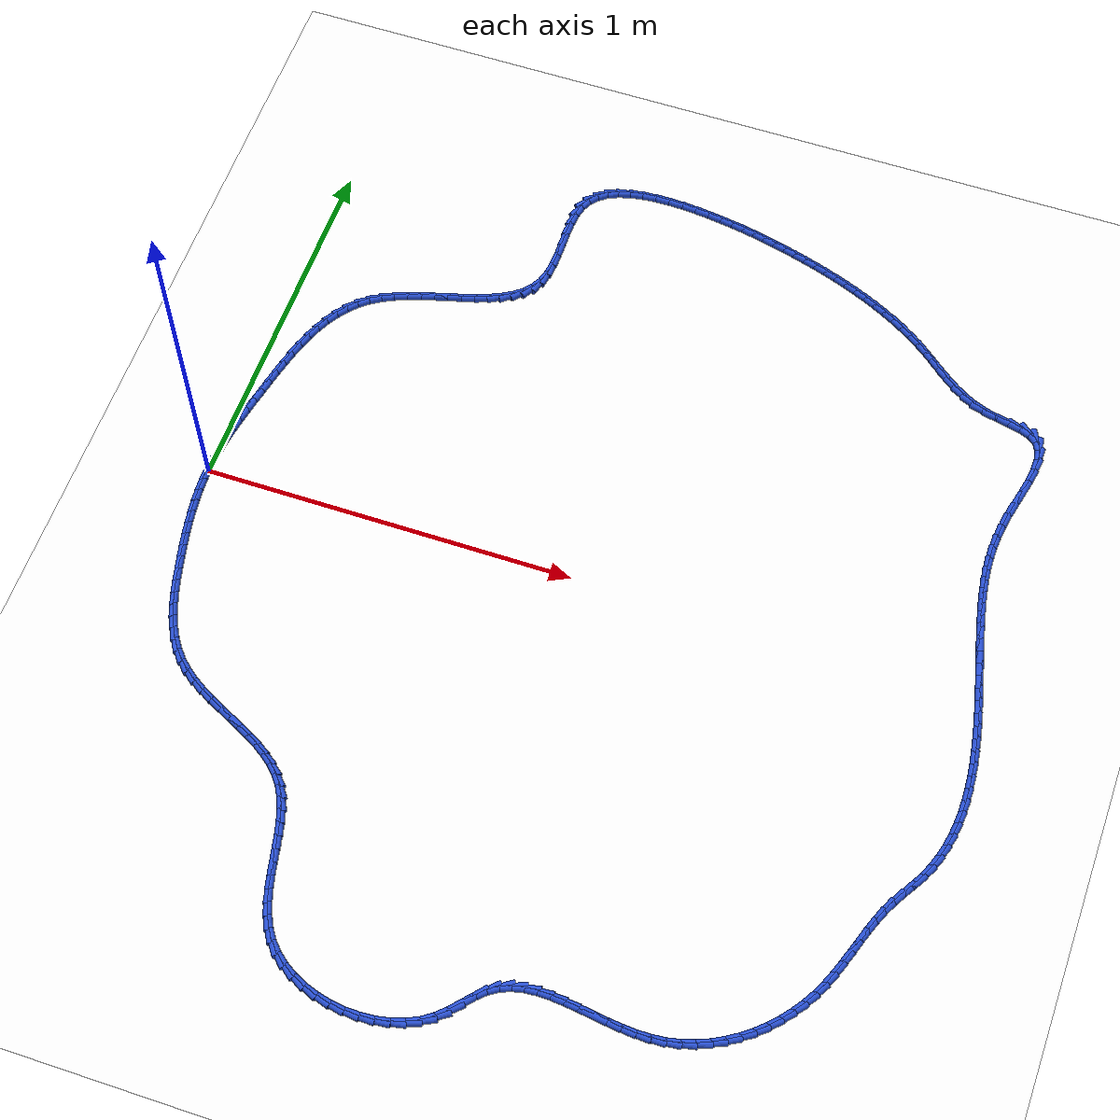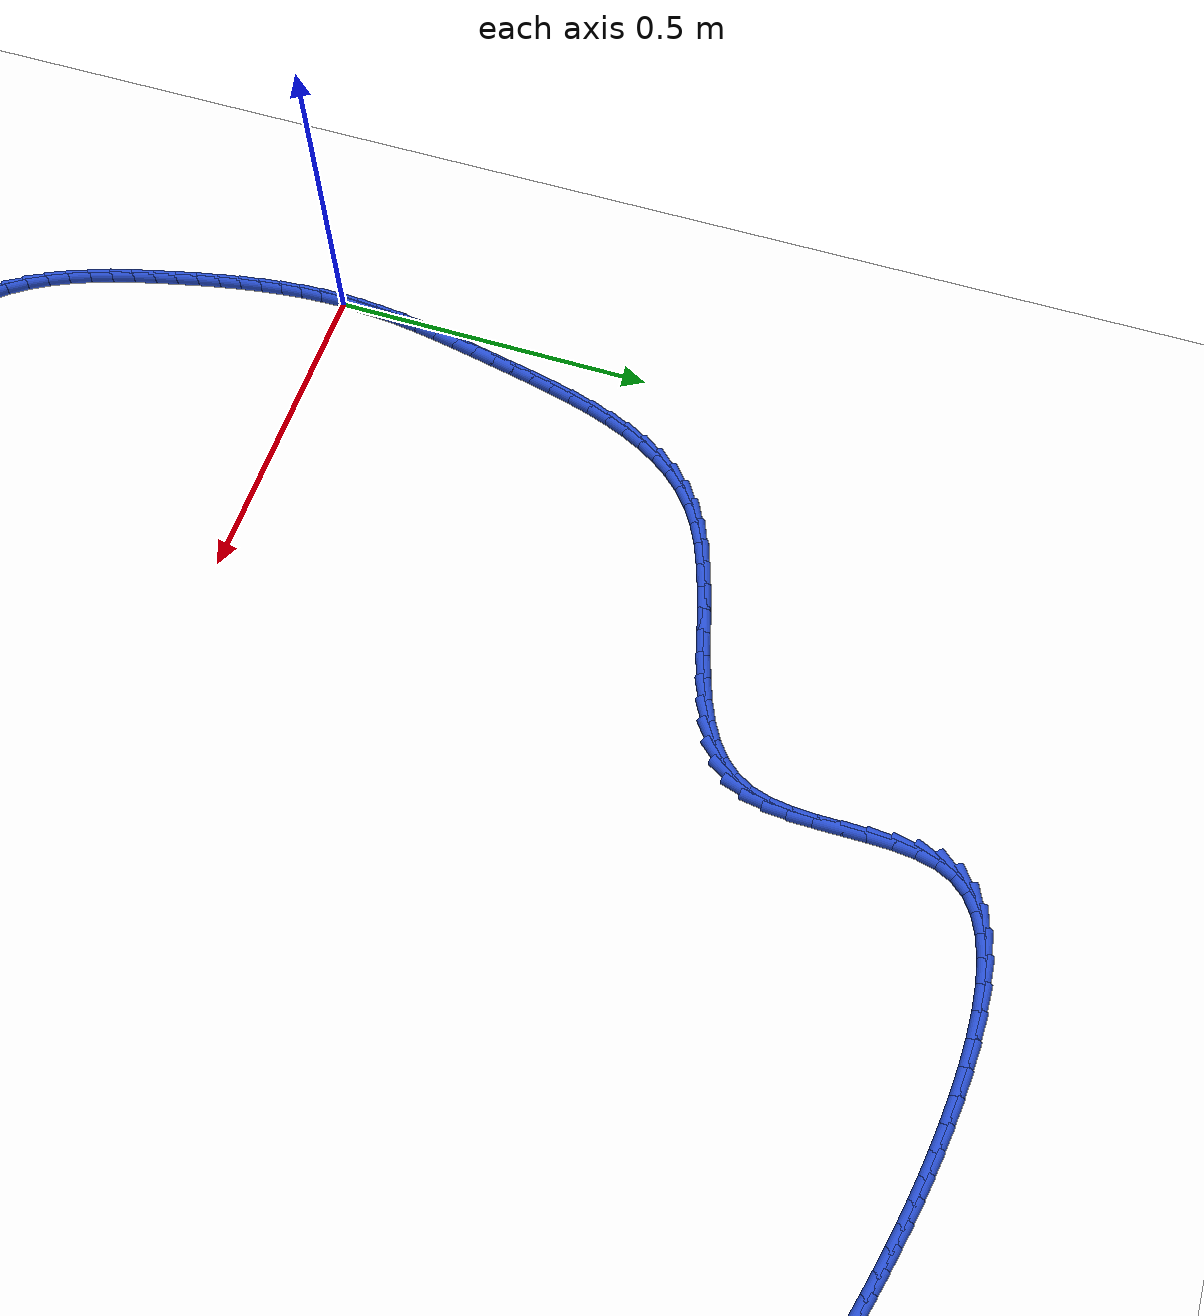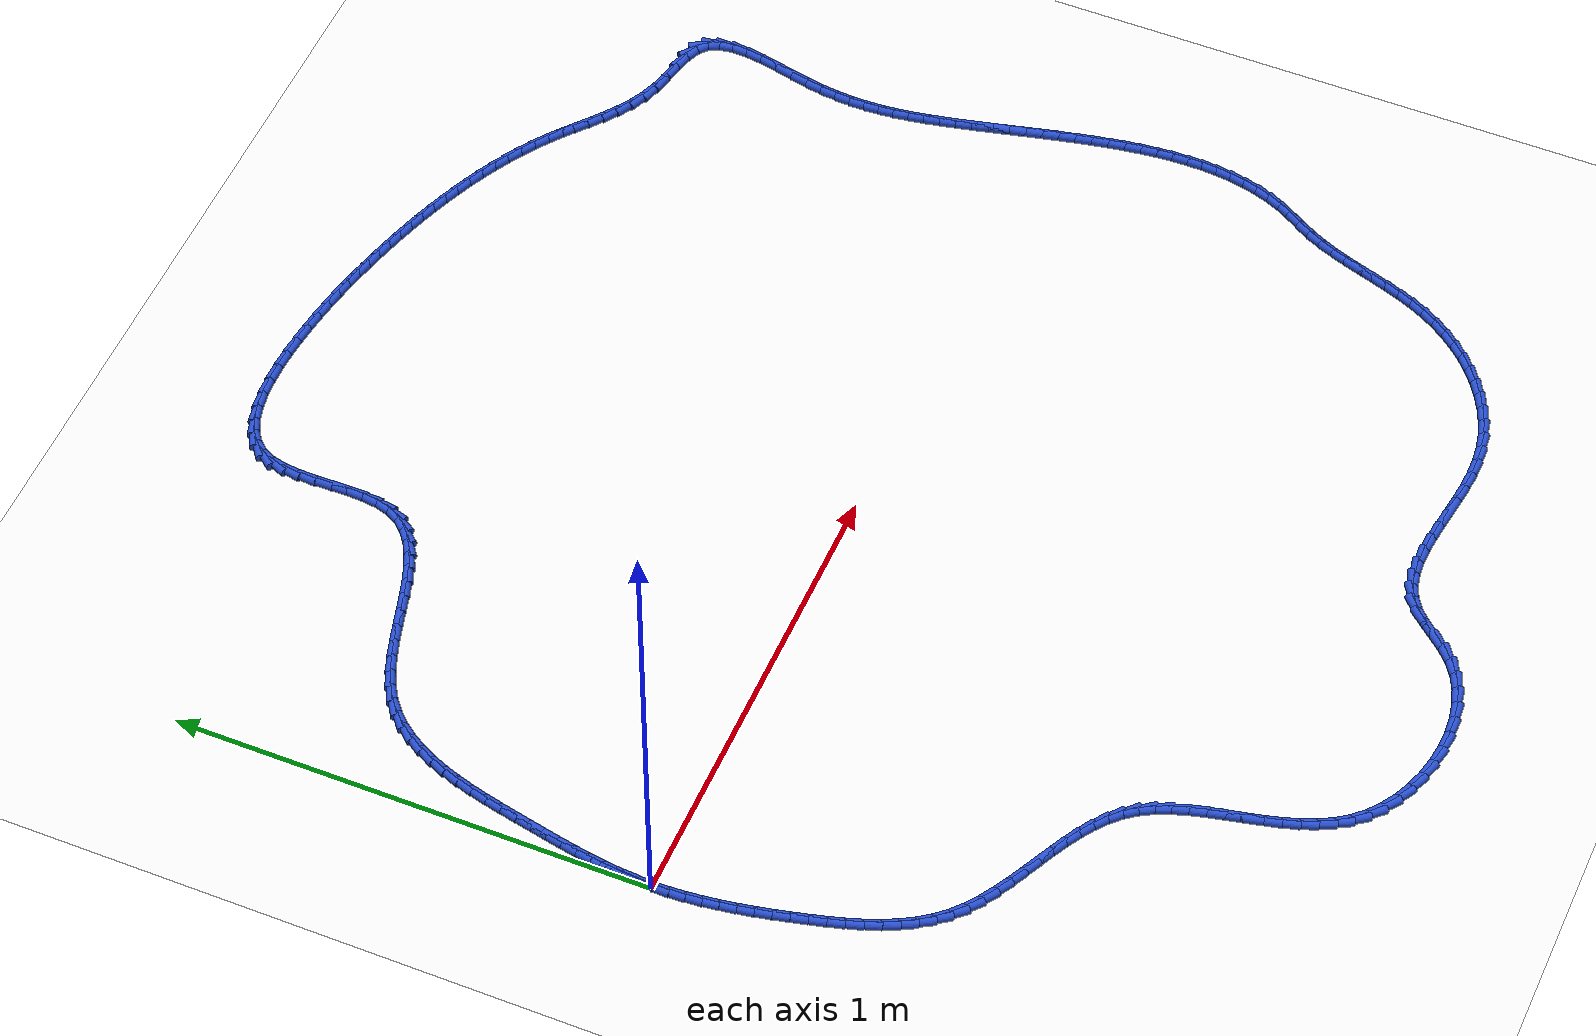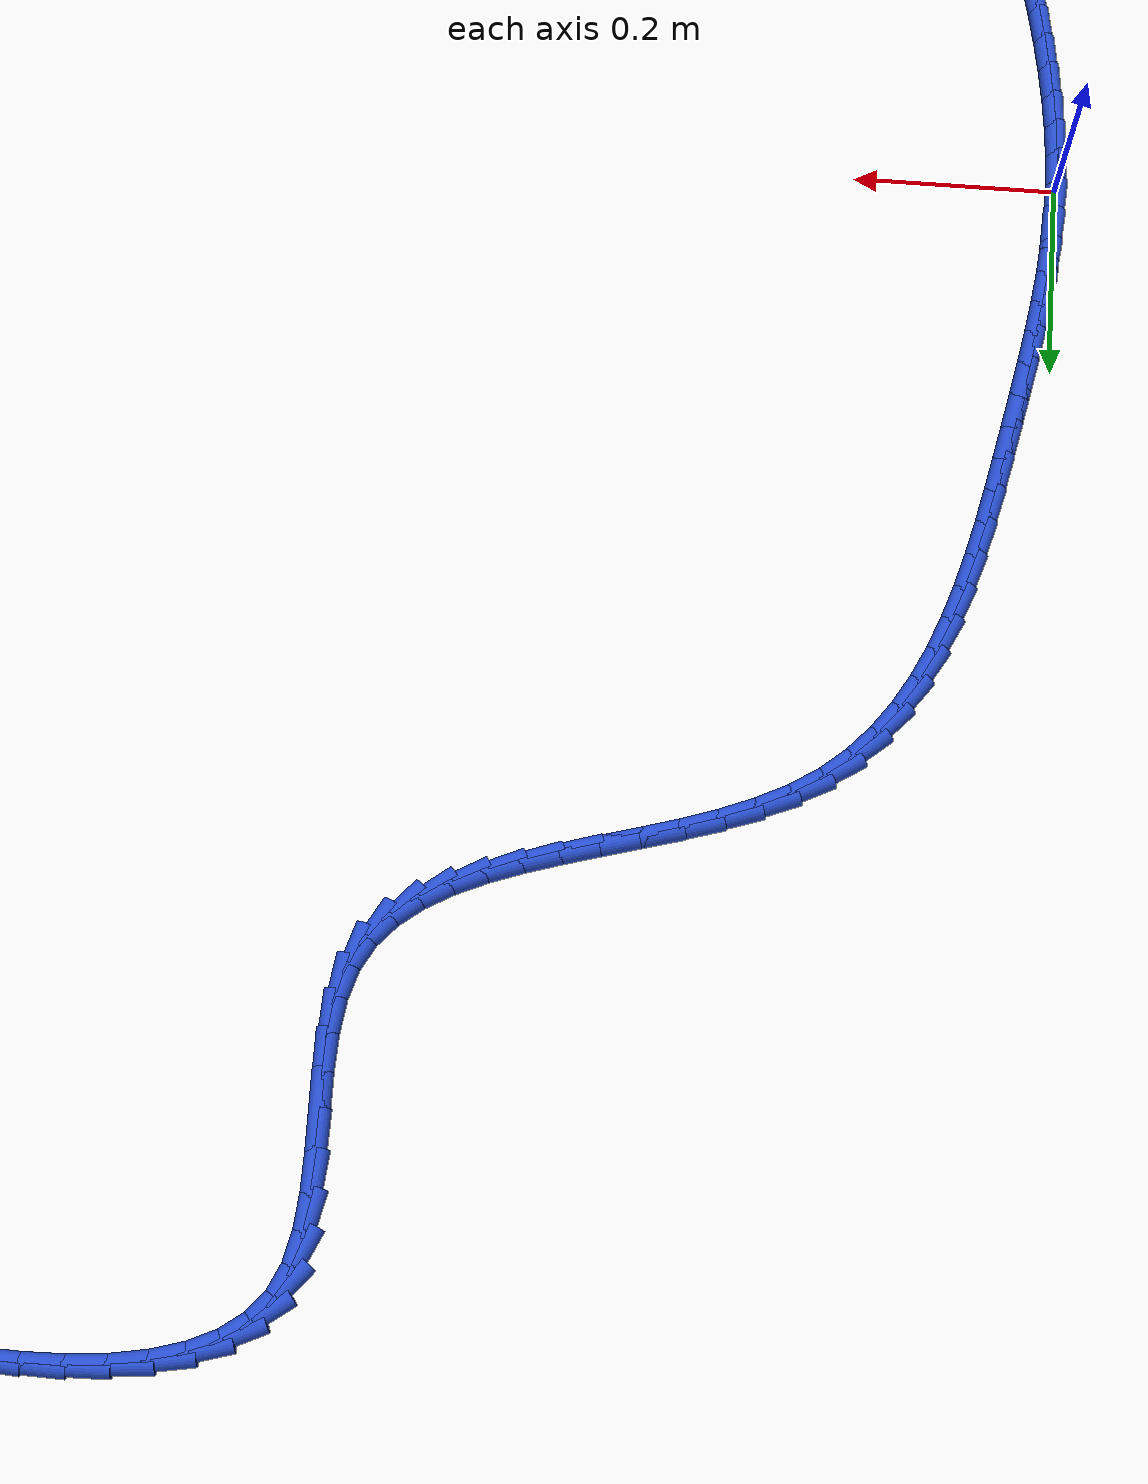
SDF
<sdf version="1.6">
 <world name="default">
  <light name="sun" type="directional">
   <pose>0 0 10 0 -0 0</pose>
   <diffuse>0.8 0.8 0.8 1</diffuse>
   <specular>0.2 0.2 0.2 1</specular>
   <attenuation>
    <range>1000</range>
    <constant>0.9</constant>
    <linear>0.01</linear>
    <quadratic>0.001</quadratic>
   </attenuation>
   <direction>-0.5 0.1 -0.9</direction>
  </light>
  <model name="ground_plane">
   <static>1</static>
   <link name="link">
    <collision name="collision">
     <geometry><plane><normal>0 0 1</normal><size>100 100</size></plane></geometry>
     <surface><friction><ode><mu>100</mu><mu2>50</mu2></ode></friction></surface>
    </collision>
    <visual name="visual">
     <cast_shadows>0</cast_shadows>
     <geometry><plane><normal>0 0 1</normal><size>100 100</size></plane></geometry>
     <material>
      <script><uri>file://media/materials/scripts/gazebo.material</uri><name>Gazebo/WhiteGlow</name></script>
     </material>
    </visual>
   </link>
  </model>
  <gravity>0 0 -9.8</gravity>
  <magnetic_field>6e-06 2.3e-05 -4.2e-05</magnetic_field>
  <atmosphere type="adiabatic"/>
  <physics name="default_physics" default="0" type="ode">
   <max_step_size>0.001</max_step_size>
   <real_time_factor>1</real_time_factor>
   <real_time_update_rate>1000</real_time_update_rate>
  </physics>
  <scene><ambient>0.4 0.4 0.4 1</ambient><background>0.7 0.7 0.7 1</background><shadows>1</shadows></scene>
  <spherical_coordinates>
   <surface_model>EARTH_WGS84</surface_model>
   <latitude_deg>0</latitude_deg>
   <longitude_deg>0</longitude_deg>
   <elevation>0</elevation>
   <heading_deg>0</heading_deg>
  </spherical_coordinates>
  <model name="line">
   <link name="link_0">
    <pose>-2.6020852139652106e-18 6.938893903907228e-18 0.01 0 1.57 1.539757953169769</pose>
    <collision name="collision">
     <geometry><cylinder><radius>0.01</radius><length>0.08</length></cylinder></geometry>
    </collision>
    <visual name="visual">
     <material>
      <script><name>Gazebo/Blue</name><uri>file://media/materials/scripts/gazebo.material</uri></script>
     </material>
     <geometry><cylinder><radius>0.01</radius><length>0.08</length></cylinder></geometry>
    </visual>
   </link>
   <link name="link_1">
    <pose>0.0010129123433304473 0.032623714801807605 0.01 0 1.57 1.4978155518894152</pose>
    <collision name="collision">
     <geometry><cylinder><radius>0.01</radius><length>0.08</length></cylinder></geometry>
    </collision>
    <visual name="visual">
     <material>
      <script><name>Gazebo/Blue</name><uri>file://media/materials/scripts/gazebo.material</uri></script>
     </material>
     <geometry><cylinder><radius>0.01</radius><length>0.08</length></cylinder></geometry>
    </visual>
   </link>
   <link name="link_2">
    <pose>0.003396929024945162 0.06523206409621125 0.01 0 1.57 1.4615119541450086</pose>
    <collision name="collision">
     <geometry><cylinder><radius>0.01</radius><length>0.08</length></cylinder></geometry>
    </collision>
    <visual name="visual">
     <material>
      <script><name>Gazebo/Blue</name><uri>file://media/materials/scripts/gazebo.material</uri></script>
     </material>
     <geometry><cylinder><radius>0.01</radius><length>0.08</length></cylinder></geometry>
    </visual>
   </link>
   <link name="link_3">
    <pose>0.006980682756064616 0.09789433098796897 0.01 0 1.57 1.4310375898183822</pose>
    <collision name="collision">
     <geometry><cylinder><radius>0.01</radius><length>0.08</length></cylinder></geometry>
    </collision>
    <visual name="visual">
     <material>
      <script><name>Gazebo/Blue</name><uri>file://media/materials/scripts/gazebo.material</uri></script>
     </material>
     <geometry><cylinder><radius>0.01</radius><length>0.08</length></cylinder></geometry>
    </visual>
   </link>
   <link name="link_4">
    <pose>0.011592806247909286 0.13067979858183865 0.01 0 1.57 1.4064502367888128</pose>
    <collision name="collision">
     <geometry><cylinder><radius>0.01</radius><length>0.08</length></cylinder></geometry>
    </collision>
    <visual name="visual">
     <material>
      <script><name>Gazebo/Blue</name><uri>file://media/materials/scripts/gazebo.material</uri></script>
     </material>
     <geometry><cylinder><radius>0.01</radius><length>0.08</length></cylinder></geometry>
    </visual>
   </link>
   <link name="link_5">
    <pose>0.017061932211699642 0.16365774998257834 0.01 0 1.57 1.387707099272295</pose>
    <collision name="collision">
     <geometry><cylinder><radius>0.01</radius><length>0.08</length></cylinder></geometry>
    </collision>
    <visual name="visual">
     <material>
      <script><name>Gazebo/Blue</name><uri>file://media/materials/scripts/gazebo.material</uri></script>
     </material>
     <geometry><cylinder><radius>0.01</radius><length>0.08</length></cylinder></geometry>
    </visual>
   </link>
   <link name="link_6">
    <pose>0.023216693358656164 0.19689746829494592 0.01 0 1.57 1.3746935659658839</pose>
    <collision name="collision">
     <geometry><cylinder><radius>0.01</radius><length>0.08</length></cylinder></geometry>
    </collision>
    <visual name="visual">
     <material>
      <script><name>Gazebo/Blue</name><uri>file://media/materials/scripts/gazebo.material</uri></script>
     </material>
     <geometry><cylinder><radius>0.01</radius><length>0.08</length></cylinder></geometry>
    </visual>
   </link>
   <link name="link_7">
    <pose>0.029885722399999315 0.2304682366236993 0.01 0 1.57 1.367246253373071</pose>
    <collision name="collision">
     <geometry><cylinder><radius>0.01</radius><length>0.08</length></cylinder></geometry>
    </collision>
    <visual name="visual">
     <material>
      <script><name>Gazebo/Blue</name><uri>file://media/materials/scripts/gazebo.material</uri></script>
     </material>
     <geometry><cylinder><radius>0.01</radius><length>0.08</length></cylinder></geometry>
    </visual>
   </link>
   <link name="link_8">
    <pose>0.0368976520469496 0.26443933807359654 0.01 0 1.57 1.3648676268723923</pose>
    <collision name="collision">
     <geometry><cylinder><radius>0.01</radius><length>0.08</length></cylinder></geometry>
    </collision>
    <visual name="visual">
     <material>
      <script><name>Gazebo/Blue</name><uri>file://media/materials/scripts/gazebo.material</uri></script>
     </material>
     <geometry><cylinder><radius>0.01</radius><length>0.08</length></cylinder></geometry>
    </visual>
   </link>
   <link name="link_9">
    <pose>0.04409036057541131 0.2988723582565609 0.01 0 1.57 1.3603636788346232</pose>
    <collision name="collision">
     <geometry><cylinder><radius>0.01</radius><length>0.08</length></cylinder></geometry>
    </collision>
    <visual name="visual">
     <material>
      <script><name>Gazebo/Blue</name><uri>file://media/materials/scripts/gazebo.material</uri></script>
     </material>
     <geometry><cylinder><radius>0.01</radius><length>0.08</length></cylinder></geometry>
    </visual>
   </link>
   <link name="link_10">
    <pose>0.051518366751977525 0.3336485164486758 0.01 0 1.57 1.3466791691757087</pose>
    <collision name="collision">
     <geometry><cylinder><radius>0.01</radius><length>0.08</length></cylinder></geometry>
    </collision>
    <visual name="visual">
     <material>
      <script><name>Gazebo/Blue</name><uri>file://media/materials/scripts/gazebo.material</uri></script>
     </material>
     <geometry><cylinder><radius>0.01</radius><length>0.08</length></cylinder></geometry>
    </visual>
   </link>
   <link name="link_11">
    <pose>0.05945507138275609 0.36846679936496035 0.01 0 1.57 1.3233494310399248</pose>
    <collision name="collision">
     <geometry><cylinder><radius>0.01</radius><length>0.08</length></cylinder></geometry>
    </collision>
    <visual name="visual">
     <material>
      <script><name>Gazebo/Blue</name><uri>file://media/materials/scripts/gazebo.material</uri></script>
     </material>
     <geometry><cylinder><radius>0.01</radius><length>0.08</length></cylinder></geometry>
    </visual>
   </link>
   <link name="link_12">
    <pose>0.06818356916319533 0.4030181229701567 0.01 0 1.57 1.2898818693365801</pose>
    <collision name="collision">
     <geometry><cylinder><radius>0.01</radius><length>0.08</length></cylinder></geometry>
    </collision>
    <visual name="visual">
     <material>
      <script><name>Gazebo/Blue</name><uri>file://media/materials/scripts/gazebo.material</uri></script>
     </material>
     <geometry><cylinder><radius>0.01</radius><length>0.08</length></cylinder></geometry>
    </visual>
   </link>
   <link name="link_13">
    <pose>0.07798695478874354 0.43699340322900615 0.01 0 1.57 1.2454784135910657</pose>
    <collision name="collision">
     <geometry><cylinder><radius>0.01</radius><length>0.08</length></cylinder></geometry>
    </collision>
    <visual name="visual">
     <material>
      <script><name>Gazebo/Blue</name><uri>file://media/materials/scripts/gazebo.material</uri></script>
     </material>
     <geometry><cylinder><radius>0.01</radius><length>0.08</length></cylinder></geometry>
    </visual>
   </link>
   <link name="link_14">
    <pose>0.08914832295484894 0.4700835561062505 0.01 0 1.57 1.1890994455133583</pose>
    <collision name="collision">
     <geometry><cylinder><radius>0.01</radius><length>0.08</length></cylinder></geometry>
    </collision>
    <visual name="visual">
     <material>
      <script><name>Gazebo/Blue</name><uri>file://media/materials/scripts/gazebo.material</uri></script>
     </material>
     <geometry><cylinder><radius>0.01</radius><length>0.08</length></cylinder></geometry>
    </visual>
   </link>
   <link name="link_15">
    <pose>0.10195076835695994 0.5019794975666315 0.01 0 1.57 1.1195886480006347</pose>
    <collision name="collision">
     <geometry><cylinder><radius>0.01</radius><length>0.08</length></cylinder></geometry>
    </collision>
    <visual name="visual">
     <material>
      <script><name>Gazebo/Blue</name><uri>file://media/materials/scripts/gazebo.material</uri></script>
     </material>
     <geometry><cylinder><radius>0.01</radius><length>0.08</length></cylinder></geometry>
    </visual>
   </link>
   <link name="link_16">
    <pose>0.11667738569052477 0.5323721435748909 0.01 0 1.57 1.0359078142784317</pose>
    <collision name="collision">
     <geometry><cylinder><radius>0.01</radius><length>0.08</length></cylinder></geometry>
    </collision>
    <visual name="visual">
     <material>
      <script><name>Gazebo/Blue</name><uri>file://media/materials/scripts/gazebo.material</uri></script>
     </material>
     <geometry><cylinder><radius>0.01</radius><length>0.08</length></cylinder></geometry>
    </visual>
   </link>
   <link name="link_17">
    <pose>0.1336112696509918 0.5609524100957706 0.01 0 1.57 0.937528538577671</pose>
    <collision name="collision">
     <geometry><cylinder><radius>0.01</radius><length>0.08</length></cylinder></geometry>
    </collision>
    <visual name="visual">
     <material>
      <script><name>Gazebo/Blue</name><uri>file://media/materials/scripts/gazebo.material</uri></script>
     </material>
     <geometry><cylinder><radius>0.01</radius><length>0.08</length></cylinder></geometry>
    </visual>
   </link>
   <link name="link_18">
    <pose>0.15303551493380918 0.5874112130940118 0.01 0 1.57 0.8249776181938494</pose>
    <collision name="collision">
     <geometry><cylinder><radius>0.01</radius><length>0.08</length></cylinder></geometry>
    </collision>
    <visual name="visual">
     <material>
      <script><name>Gazebo/Blue</name><uri>file://media/materials/scripts/gazebo.material</uri></script>
     </material>
     <geometry><cylinder><radius>0.01</radius><length>0.08</length></cylinder></geometry>
    </visual>
   </link>
   <link name="link_19">
    <pose>0.1752332162344254 0.6114394685343565 0.01 0 1.57 0.7003996909303799</pose>
    <collision name="collision">
     <geometry><cylinder><radius>0.01</radius><length>0.08</length></cylinder></geometry>
    </collision>
    <visual name="visual">
     <material>
      <script><name>Gazebo/Blue</name><uri>file://media/materials/scripts/gazebo.material</uri></script>
     </material>
     <geometry><cylinder><radius>0.01</radius><length>0.08</length></cylinder></geometry>
    </visual>
   </link>
   <link name="link_20">
    <pose>0.20048746824828861 0.6327280923815465 0.01 0 1.57 0.5706910542830176</pose>
    <collision name="collision">
     <geometry><cylinder><radius>0.01</radius><length>0.08</length></cylinder></geometry>
    </collision>
    <visual name="visual">
     <material>
      <script><name>Gazebo/Blue</name><uri>file://media/materials/scripts/gazebo.material</uri></script>
     </material>
     <geometry><cylinder><radius>0.01</radius><length>0.08</length></cylinder></geometry>
    </visual>
   </link>
   <link name="link_21">
    <pose>0.22900621415514796 0.6510355288182952 0.01 0 1.57 0.46151577903712626</pose>
    <collision name="collision">
     <geometry><cylinder><radius>0.01</radius><length>0.08</length></cylinder></geometry>
    </collision>
    <visual name="visual">
     <material>
      <script><name>Gazebo/Blue</name><uri>file://media/materials/scripts/gazebo.material</uri></script>
     </material>
     <geometry><cylinder><radius>0.01</radius><length>0.08</length></cylinder></geometry>
    </visual>
   </link>
   <link name="link_22">
    <pose>0.2604058505984582 0.6666517626499088 0.01 0 1.57 0.3810138606256112</pose>
    <collision name="collision">
     <geometry><cylinder><radius>0.01</radius><length>0.08</length></cylinder></geometry>
    </collision>
    <visual name="visual">
     <material>
      <script><name>Gazebo/Blue</name><uri>file://media/materials/scripts/gazebo.material</uri></script>
     </material>
     <geometry><cylinder><radius>0.01</radius><length>0.08</length></cylinder></geometry>
    </visual>
   </link>
   <link name="link_23">
    <pose>0.29402281270156605 0.6801183411735161 0.01 0 1.57 0.3252512268479439</pose>
    <collision name="collision">
     <geometry><cylinder><radius>0.01</radius><length>0.08</length></cylinder></geometry>
    </collision>
    <visual name="visual">
     <material>
      <script><name>Gazebo/Blue</name><uri>file://media/materials/scripts/gazebo.material</uri></script>
     </material>
     <geometry><cylinder><radius>0.01</radius><length>0.08</length></cylinder></geometry>
    </visual>
   </link>
   <link name="link_24">
    <pose>0.32919186420682534 0.6919783135239546 0.01 0 1.57 0.29093875988159834</pose>
    <collision name="collision">
     <geometry><cylinder><radius>0.01</radius><length>0.08</length></cylinder></geometry>
    </collision>
    <visual name="visual">
     <material>
      <script><name>Gazebo/Blue</name><uri>file://media/materials/scripts/gazebo.material</uri></script>
     </material>
     <geometry><cylinder><radius>0.01</radius><length>0.08</length></cylinder></geometry>
    </visual>
   </link>
   <link name="link_25">
    <pose>0.3652477688565897 0.7027747288360604 0.01 0 1.57 0.2760275179680214</pose>
    <collision name="collision">
     <geometry><cylinder><radius>0.01</radius><length>0.08</length></cylinder></geometry>
    </collision>
    <visual name="visual">
     <material>
      <script><name>Gazebo/Blue</name><uri>file://media/materials/scripts/gazebo.material</uri></script>
     </material>
     <geometry><cylinder><radius>0.01</radius><length>0.08</length></cylinder></geometry>
    </visual>
   </link>
   <link name="link_26">
    <pose>0.40152529039321316 0.7130506362446701 0.01 0 1.57 0.2798519165697917</pose>
    <collision name="collision">
     <geometry><cylinder><radius>0.01</radius><length>0.08</length></cylinder></geometry>
    </collision>
    <visual name="visual">
     <material>
      <script><name>Gazebo/Blue</name><uri>file://media/materials/scripts/gazebo.material</uri></script>
     </material>
     <geometry><cylinder><radius>0.01</radius><length>0.08</length></cylinder></geometry>
    </visual>
   </link>
   <link name="link_27">
    <pose>0.4373591925590492 0.7233490848846201 0.01 0 1.57 0.3032117818992688</pose>
    <collision name="collision">
     <geometry><cylinder><radius>0.01</radius><length>0.08</length></cylinder></geometry>
    </collision>
    <visual name="visual">
     <material>
      <script><name>Gazebo/Blue</name><uri>file://media/materials/scripts/gazebo.material</uri></script>
     </material>
     <geometry><cylinder><radius>0.01</radius><length>0.08</length></cylinder></geometry>
    </visual>
   </link>
   <link name="link_28">
    <pose>0.47208423909645153 0.7342131238907471 0.01 0 1.57 0.348516696978663</pose>
    <collision name="collision">
     <geometry><cylinder><radius>0.01</radius><length>0.08</length></cylinder></geometry>
    </collision>
    <visual name="visual">
     <material>
      <script><name>Gazebo/Blue</name><uri>file://media/materials/scripts/gazebo.material</uri></script>
     </material>
     <geometry><cylinder><radius>0.01</radius><length>0.08</length></cylinder></geometry>
    </visual>
   </link>
   <link name="link_29">
    <pose>0.5050351937477742 0.7461858023978878 0.01 0 1.57 0.41996481578611994</pose>
    <collision name="collision">
     <geometry><cylinder><radius>0.01</radius><length>0.08</length></cylinder></geometry>
    </collision>
    <visual name="visual">
     <material>
      <script><name>Gazebo/Blue</name><uri>file://media/materials/scripts/gazebo.material</uri></script>
     </material>
     <geometry><cylinder><radius>0.01</radius><length>0.08</length></cylinder></geometry>
    </visual>
   </link>
   <link name="link_30">
    <pose>0.5355468202553707 0.7598101695408782 0.01 0 1.57 0.5234791876418031</pose>
    <collision name="collision">
     <geometry><cylinder><radius>0.01</radius><length>0.08</length></cylinder></geometry>
    </collision>
    <visual name="visual">
     <material>
      <script><name>Gazebo/Blue</name><uri>file://media/materials/scripts/gazebo.material</uri></script>
     </material>
     <geometry><cylinder><radius>0.01</radius><length>0.08</length></cylinder></geometry>
    </visual>
   </link>
   <link name="link_31">
    <pose>0.562953882361595 0.7756292744545554 0.01 0 1.57 0.6655704121327519</pose>
    <collision name="collision">
     <geometry><cylinder><radius>0.01</radius><length>0.08</length></cylinder></geometry>
    </collision>
    <visual name="visual">
     <material>
      <script><name>Gazebo/Blue</name><uri>file://media/materials/scripts/gazebo.material</uri></script>
     </material>
     <geometry><cylinder><radius>0.01</radius><length>0.08</length></cylinder></geometry>
    </visual>
   </link>
   <link name="link_32">
    <pose>0.5865911438088007 0.7941861662737557 0.01 0 1.57 0.849528095786038</pose>
    <collision name="collision">
     <geometry><cylinder><radius>0.01</radius><length>0.08</length></cylinder></geometry>
    </collision>
    <visual name="visual">
     <material>
      <script><name>Gazebo/Blue</name><uri>file://media/materials/scripts/gazebo.material</uri></script>
     </material>
     <geometry><cylinder><radius>0.01</radius><length>0.08</length></cylinder></geometry>
    </visual>
   </link>
   <link name="link_33">
    <pose>0.6057933683393417 0.8160238941333157 0.01 0 1.57 1.0683102863868055</pose>
    <collision name="collision">
     <geometry><cylinder><radius>0.01</radius><length>0.08</length></cylinder></geometry>
    </collision>
    <visual name="visual">
     <material>
      <script><name>Gazebo/Blue</name><uri>file://media/materials/scripts/gazebo.material</uri></script>
     </material>
     <geometry><cylinder><radius>0.01</radius><length>0.08</length></cylinder></geometry>
    </visual>
   </link>
   <link name="link_34">
    <pose>0.6198953196955717 0.8416855071680718 0.01 0 1.57 1.287420169686413</pose>
    <collision name="collision">
     <geometry><cylinder><radius>0.01</radius><length>0.08</length></cylinder></geometry>
    </collision>
    <visual name="visual">
     <material>
      <script><name>Gazebo/Blue</name><uri>file://media/materials/scripts/gazebo.material</uri></script>
     </material>
     <geometry><cylinder><radius>0.01</radius><length>0.08</length></cylinder></geometry>
    </visual>
   </link>
   <link name="link_35">
    <pose>0.6285639003954384 0.8714526339926593 0.01 0 1.57 1.4427060322493577</pose>
    <collision name="collision">
     <geometry><cylinder><radius>0.01</radius><length>0.08</length></cylinder></geometry>
    </collision>
    <visual name="visual">
     <material>
      <script><name>Gazebo/Blue</name><uri>file://media/materials/scripts/gazebo.material</uri></script>
     </material>
     <geometry><cylinder><radius>0.01</radius><length>0.08</length></cylinder></geometry>
    </visual>
   </link>
   <link name="link_36">
    <pose>0.6328250462500513 0.9045372322992693 0.01 0 1.57 1.5360852553855275</pose>
    <collision name="collision">
     <geometry><cylinder><radius>0.01</radius><length>0.08</length></cylinder></geometry>
    </collision>
    <visual name="visual">
     <material>
      <script><name>Gazebo/Blue</name><uri>file://media/materials/scripts/gazebo.material</uri></script>
     </material>
     <geometry><cylinder><radius>0.01</radius><length>0.08</length></cylinder></geometry>
    </visual>
   </link>
   <link name="link_37">
    <pose>0.6340522449286653 0.9398777078968759 0.01 0 1.57 -1.558938020085584</pose>
    <collision name="collision">
     <geometry><cylinder><radius>0.01</radius><length>0.08</length></cylinder></geometry>
    </collision>
    <visual name="visual">
     <material>
      <script><name>Gazebo/Blue</name><uri>file://media/materials/scripts/gazebo.material</uri></script>
     </material>
     <geometry><cylinder><radius>0.01</radius><length>0.08</length></cylinder></geometry>
    </visual>
   </link>
   <link name="link_38">
    <pose>0.6336189842473676 0.9764124664788819 0.01 0 1.57 -1.5511565734463788</pose>
    <collision name="collision">
     <geometry><cylinder><radius>0.01</radius><length>0.08</length></cylinder></geometry>
    </collision>
    <visual name="visual">
     <material>
      <script><name>Gazebo/Blue</name><uri>file://media/materials/scripts/gazebo.material</uri></script>
     </material>
     <geometry><cylinder><radius>0.01</radius><length>0.08</length></cylinder></geometry>
    </visual>
   </link>
   <link name="link_39">
    <pose>0.6328987520222471 1.013079913738692 0.01 0 1.57 1.5605476930738251</pose>
    <collision name="collision">
     <geometry><cylinder><radius>0.01</radius><length>0.08</length></cylinder></geometry>
    </collision>
    <visual name="visual">
     <material>
      <script><name>Gazebo/Blue</name><uri>file://media/materials/scripts/gazebo.material</uri></script>
     </material>
     <geometry><cylinder><radius>0.01</radius><length>0.08</length></cylinder></geometry>
    </visual>
   </link>
   <link name="link_40">
    <pose>0.6332650360693916 1.0488184553697102 0.01 0 1.57 1.4872445633317386</pose>
    <collision name="collision">
     <geometry><cylinder><radius>0.01</radius><length>0.08</length></cylinder></geometry>
    </collision>
    <visual name="visual">
     <material>
      <script><name>Gazebo/Blue</name><uri>file://media/materials/scripts/gazebo.material</uri></script>
     </material>
     <geometry><cylinder><radius>0.01</radius><length>0.08</length></cylinder></geometry>
    </visual>
   </link>
   <link name="link_41">
    <pose>0.6360913242048886 1.0825664970653393 0.01 0 1.57 1.3571479169844467</pose>
    <collision name="collision">
     <geometry><cylinder><radius>0.01</radius><length>0.08</length></cylinder></geometry>
    </collision>
    <visual name="visual">
     <material>
      <script><name>Gazebo/Blue</name><uri>file://media/materials/scripts/gazebo.material</uri></script>
     </material>
     <geometry><cylinder><radius>0.01</radius><length>0.08</length></cylinder></geometry>
    </visual>
   </link>
   <link name="link_42">
    <pose>0.6427511042448266 1.1132624445189838 0.01 0 1.57 1.1509646233116997</pose>
    <collision name="collision">
     <geometry><cylinder><radius>0.01</radius><length>0.08</length></cylinder></geometry>
    </collision>
    <visual name="visual">
     <material>
      <script><name>Gazebo/Blue</name><uri>file://media/materials/scripts/gazebo.material</uri></script>
     </material>
     <geometry><cylinder><radius>0.01</radius><length>0.08</length></cylinder></geometry>
    </visual>
   </link>
   <link name="link_43">
    <pose>0.6546169300186753 1.139845340123677 0.01 0 1.57 0.8822303728471826</pose>
    <collision name="collision">
     <geometry><cylinder><radius>0.01</radius><length>0.08</length></cylinder></geometry>
    </collision>
    <visual name="visual">
     <material>
      <script><name>Gazebo/Blue</name><uri>file://media/materials/scripts/gazebo.material</uri></script>
     </material>
     <geometry><cylinder><radius>0.01</radius><length>0.08</length></cylinder></geometry>
    </visual>
   </link>
   <link name="link_44">
    <pose>0.6725319146698112 1.1616151465278655 0.01 0 1.57 0.6345131346211561</pose>
    <collision name="collision">
     <geometry><cylinder><radius>0.01</radius><length>0.08</length></cylinder></geometry>
    </collision>
    <visual name="visual">
     <material>
      <script><name>Gazebo/Blue</name><uri>file://media/materials/scripts/gazebo.material</uri></script>
     </material>
     <geometry><cylinder><radius>0.01</radius><length>0.08</length></cylinder></geometry>
    </visual>
   </link>
   <link name="link_45">
    <pose>0.6959265817796008 1.1788347901243885 0.01 0 1.57 0.43636633583716566</pose>
    <collision name="collision">
     <geometry><cylinder><radius>0.01</radius><length>0.08</length></cylinder></geometry>
    </collision>
    <visual name="visual">
     <material>
      <script><name>Gazebo/Blue</name><uri>file://media/materials/scripts/gazebo.material</uri></script>
     </material>
     <geometry><cylinder><radius>0.01</radius><length>0.08</length></cylinder></geometry>
    </visual>
   </link>
   <link name="link_46">
    <pose>0.7239984125193261 1.1919260625545993 0.01 0 1.57 0.2857250114022844</pose>
    <collision name="collision">
     <geometry><cylinder><radius>0.01</radius><length>0.08</length></cylinder></geometry>
    </collision>
    <visual name="visual">
     <material>
      <script><name>Gazebo/Blue</name><uri>file://media/materials/scripts/gazebo.material</uri></script>
     </material>
     <geometry><cylinder><radius>0.01</radius><length>0.08</length></cylinder></geometry>
    </visual>
   </link>
   <link name="link_47">
    <pose>0.7559448880602689 1.2013107554598517 0.01 0 1.57 0.17246003848919886</pose>
    <collision name="collision">
     <geometry><cylinder><radius>0.01</radius><length>0.08</length></cylinder></geometry>
    </collision>
    <visual name="visual">
     <material>
      <script><name>Gazebo/Blue</name><uri>file://media/materials/scripts/gazebo.material</uri></script>
     </material>
     <geometry><cylinder><radius>0.01</radius><length>0.08</length></cylinder></geometry>
    </visual>
   </link>
   <link name="link_48">
    <pose>0.7909634895737117 1.207410660481499 0.01 0 1.57 0.08659076894878517</pose>
    <collision name="collision">
     <geometry><cylinder><radius>0.01</radius><length>0.08</length></cylinder></geometry>
    </collision>
    <visual name="visual">
     <material>
      <script><name>Gazebo/Blue</name><uri>file://media/materials/scripts/gazebo.material</uri></script>
     </material>
     <geometry><cylinder><radius>0.01</radius><length>0.08</length></cylinder></geometry>
    </visual>
   </link>
   <link name="link_49">
    <pose>0.8282516982309359 1.210647569260895 0.01 0 1.57 0.02052861057125366</pose>
    <collision name="collision">
     <geometry><cylinder><radius>0.01</radius><length>0.08</length></cylinder></geometry>
    </collision>
    <visual name="visual">
     <material>
      <script><name>Gazebo/Blue</name><uri>file://media/materials/scripts/gazebo.material</uri></script>
     </material>
     <geometry><cylinder><radius>0.01</radius><length>0.08</length></cylinder></geometry>
    </visual>
   </link>
   <link name="link_50">
    <pose>0.8670069952032238 1.2114432734393927 0.01 0 1.57 -0.031032979979459918</pose>
    <collision name="collision">
     <geometry><cylinder><radius>0.01</radius><length>0.08</length></cylinder></geometry>
    </collision>
    <visual name="visual">
     <material>
      <script><name>Gazebo/Blue</name><uri>file://media/materials/scripts/gazebo.material</uri></script>
     </material>
     <geometry><cylinder><radius>0.01</radius><length>0.08</length></cylinder></geometry>
    </visual>
   </link>
   <link name="link_51">
    <pose>0.9064268616618569 1.2102195646583462 0.01 0 1.57 -0.0716994994099964</pose>
    <collision name="collision">
     <geometry><cylinder><radius>0.01</radius><length>0.08</length></cylinder></geometry>
    </collision>
    <visual name="visual">
     <material>
      <script><name>Gazebo/Blue</name><uri>file://media/materials/scripts/gazebo.material</uri></script>
     </material>
     <geometry><cylinder><radius>0.01</radius><length>0.08</length></cylinder></geometry>
    </visual>
   </link>
   <link name="link_52">
    <pose>0.9457087787781174 1.2073982345591083 0.01 0 1.57 -0.10387642269641931</pose>
    <collision name="collision">
     <geometry><cylinder><radius>0.01</radius><length>0.08</length></cylinder></geometry>
    </collision>
    <visual name="visual">
     <material>
      <script><name>Gazebo/Blue</name><uri>file://media/materials/scripts/gazebo.material</uri></script>
     </material>
     <geometry><cylinder><radius>0.01</radius><length>0.08</length></cylinder></geometry>
    </visual>
   </link>
   <link name="link_53">
    <pose>0.9840502277232878 1.2034010747830337 0.01 0 1.57 -0.12918347361894353</pose>
    <collision name="collision">
     <geometry><cylinder><radius>0.01</radius><length>0.08</length></cylinder></geometry>
    </collision>
    <visual name="visual">
     <material>
      <script><name>Gazebo/Blue</name><uri>file://media/materials/scripts/gazebo.material</uri></script>
     </material>
     <geometry><cylinder><radius>0.01</radius><length>0.08</length></cylinder></geometry>
    </visual>
   </link>
   <link name="link_54">
    <pose>1.0206646947996745 1.1986446019980588 0.01 0 1.57 -0.1512373208761898</pose>
    <collision name="collision">
     <geometry><cylinder><radius>0.01</radius><length>0.08</length></cylinder></geometry>
    </collision>
    <visual name="visual">
     <material>
      <script><name>Gazebo/Blue</name><uri>file://media/materials/scripts/gazebo.material</uri></script>
     </material>
     <geometry><cylinder><radius>0.01</radius><length>0.08</length></cylinder></geometry>
    </visual>
   </link>
   <link name="link_55">
    <pose>1.0553173925527566 1.193363494856494 0.01 0 1.57 -0.17313168465110418</pose>
    <collision name="collision">
     <geometry><cylinder><radius>0.01</radius><length>0.08</length></cylinder></geometry>
    </collision>
    <visual name="visual">
     <material>
      <script><name>Gazebo/Blue</name><uri>file://media/materials/scripts/gazebo.material</uri></script>
     </material>
     <geometry><cylinder><radius>0.01</radius><length>0.08</length></cylinder></geometry>
    </visual>
   </link>
   <link name="link_56">
    <pose>1.0884519486182331 1.187568839866349 0.01 0 1.57 -0.19411385612958476</pose>
    <collision name="collision">
     <geometry><cylinder><radius>0.01</radius><length>0.08</length></cylinder></geometry>
    </collision>
    <visual name="visual">
     <material>
      <script><name>Gazebo/Blue</name><uri>file://media/materials/scripts/gazebo.material</uri></script>
     </material>
     <geometry><cylinder><radius>0.01</radius><length>0.08</length></cylinder></geometry>
    </visual>
   </link>
   <link name="link_57">
    <pose>1.120553673395602 1.1812579857242653 0.01 0 1.57 -0.2131555409797598</pose>
    <collision name="collision">
     <geometry><cylinder><radius>0.01</radius><length>0.08</length></cylinder></geometry>
    </collision>
    <visual name="visual">
     <material>
      <script><name>Gazebo/Blue</name><uri>file://media/materials/scripts/gazebo.material</uri></script>
     </material>
     <geometry><cylinder><radius>0.01</radius><length>0.08</length></cylinder></geometry>
    </visual>
   </link>
   <link name="link_58">
    <pose>1.1521078772843614 1.1744282811268842 0.01 0 1.57 -0.2293304754180516</pose>
    <collision name="collision">
     <geometry><cylinder><radius>0.01</radius><length>0.08</length></cylinder></geometry>
    </collision>
    <visual name="visual">
     <material>
      <script><name>Gazebo/Blue</name><uri>file://media/materials/scripts/gazebo.material</uri></script>
     </material>
     <geometry><cylinder><radius>0.01</radius><length>0.08</length></cylinder></geometry>
    </visual>
   </link>
   <link name="link_59">
    <pose>1.1835991958256602 1.1670770345501822 0.01 0 1.57 -0.24337684750250377</pose>
    <collision name="collision">
     <geometry><cylinder><radius>0.01</radius><length>0.08</length></cylinder></geometry>
    </collision>
    <visual name="visual">
     <material>
      <script><name>Gazebo/Blue</name><uri>file://media/materials/scripts/gazebo.material</uri></script>
     </material>
     <geometry><cylinder><radius>0.01</radius><length>0.08</length></cylinder></geometry>
    </visual>
   </link>
   <link name="link_60">
    <pose>1.2153547607505166 1.1591921674510592 0.01 0 1.57 -0.2583178332389964</pose>
    <collision name="collision">
     <geometry><cylinder><radius>0.01</radius><length>0.08</length></cylinder></geometry>
    </collision>
    <visual name="visual">
     <material>
      <script><name>Gazebo/Blue</name><uri>file://media/materials/scripts/gazebo.material</uri></script>
     </material>
     <geometry><cylinder><radius>0.01</radius><length>0.08</length></cylinder></geometry>
    </visual>
   </link>
   <link name="link_61">
    <pose>1.2473429243875163 1.1507402185078575 0.01 0 1.57 -0.27463583548799975</pose>
    <collision name="collision">
     <geometry><cylinder><radius>0.01</radius><length>0.08</length></cylinder></geometry>
    </collision>
    <visual name="visual">
     <material>
      <script><name>Gazebo/Blue</name><uri>file://media/materials/scripts/gazebo.material</uri></script>
     </material>
     <geometry><cylinder><radius>0.01</radius><length>0.08</length></cylinder></geometry>
    </visual>
   </link>
   <link name="link_62">
    <pose>1.2794823311002603 1.1416847638698542 0.01 0 1.57 -0.292384979813822</pose>
    <collision name="collision">
     <geometry><cylinder><radius>0.01</radius><length>0.08</length></cylinder></geometry>
    </collision>
    <visual name="visual">
     <material>
      <script><name>Gazebo/Blue</name><uri>file://media/materials/scripts/gazebo.material</uri></script>
     </material>
     <geometry><cylinder><radius>0.01</radius><length>0.08</length></cylinder></geometry>
    </visual>
   </link>
   <link name="link_63">
    <pose>1.3116916252523507 1.1319893796863252 0.01 0 1.57 -0.31162972916830767</pose>
    <collision name="collision">
     <geometry><cylinder><radius>0.01</radius><length>0.08</length></cylinder></geometry>
    </collision>
    <visual name="visual">
     <material>
      <script><name>Gazebo/Blue</name><uri>file://media/materials/scripts/gazebo.material</uri></script>
     </material>
     <geometry><cylinder><radius>0.01</radius><length>0.08</length></cylinder></geometry>
    </visual>
   </link>
   <link name="link_64">
    <pose>1.3438894512073882 1.1216176421065471 0.01 0 1.57 -0.33244425735694993</pose>
    <collision name="collision">
     <geometry><cylinder><radius>0.01</radius><length>0.08</length></cylinder></geometry>
    </collision>
    <visual name="visual">
     <material>
      <script><name>Gazebo/Blue</name><uri>file://media/materials/scripts/gazebo.material</uri></script>
     </material>
     <geometry><cylinder><radius>0.01</radius><length>0.08</length></cylinder></geometry>
    </visual>
   </link>
   <link name="link_65">
    <pose>1.3759944533289756 1.1105331272797967 0.01 0 1.57 -0.35491178128516054</pose>
    <collision name="collision">
     <geometry><cylinder><radius>0.01</radius><length>0.08</length></cylinder></geometry>
    </collision>
    <visual name="visual">
     <material>
      <script><name>Gazebo/Blue</name><uri>file://media/materials/scripts/gazebo.material</uri></script>
     </material>
     <geometry><cylinder><radius>0.01</radius><length>0.08</length></cylinder></geometry>
    </visual>
   </link>
   <link name="link_66">
    <pose>1.407925275980714 1.0986994113553503 0.01 0 1.57 -0.3791237536900243</pose>
    <collision name="collision">
     <geometry><cylinder><radius>0.01</radius><length>0.08</length></cylinder></geometry>
    </collision>
    <visual name="visual">
     <material>
      <script><name>Gazebo/Blue</name><uri>file://media/materials/scripts/gazebo.material</uri></script>
     </material>
     <geometry><cylinder><radius>0.01</radius><length>0.08</length></cylinder></geometry>
    </visual>
   </link>
   <link name="link_67">
    <pose>1.4396005635262041 1.0860800704824842 0.01 0 1.57 -0.4051788071473947</pose>
    <collision name="collision">
     <geometry><cylinder><radius>0.01</radius><length>0.08</length></cylinder></geometry>
    </collision>
    <visual name="visual">
     <material>
      <script><name>Gazebo/Blue</name><uri>file://media/materials/scripts/gazebo.material</uri></script>
     </material>
     <geometry><cylinder><radius>0.01</radius><length>0.08</length></cylinder></geometry>
    </visual>
   </link>
   <link name="link_68">
    <pose>1.4709389603290495 1.0726386808104753 0.01 0 1.57 -0.43318132545705185</pose>
    <collision name="collision">
     <geometry><cylinder><radius>0.01</radius><length>0.08</length></cylinder></geometry>
    </collision>
    <visual name="visual">
     <material>
      <script><name>Gazebo/Blue</name><uri>file://media/materials/scripts/gazebo.material</uri></script>
     </material>
     <geometry><cylinder><radius>0.01</radius><length>0.08</length></cylinder></geometry>
    </visual>
   </link>
   <link name="link_69">
    <pose>1.5018591107528498 1.0583388184885996 0.01 0 1.57 -0.463239502043332</pose>
    <collision name="collision">
     <geometry><cylinder><radius>0.01</radius><length>0.08</length></cylinder></geometry>
    </collision>
    <visual name="visual">
     <material>
      <script><name>Gazebo/Blue</name><uri>file://media/materials/scripts/gazebo.material</uri></script>
     </material>
     <geometry><cylinder><radius>0.01</radius><length>0.08</length></cylinder></geometry>
    </visual>
   </link>
   <link name="link_70">
    <pose>1.5322796591612082 1.0431440596661337 0.01 0 1.57 -0.495462729909424</pose>
    <collision name="collision">
     <geometry><cylinder><radius>0.01</radius><length>0.08</length></cylinder></geometry>
    </collision>
    <visual name="visual">
     <material>
      <script><name>Gazebo/Blue</name><uri>file://media/materials/scripts/gazebo.material</uri></script>
     </material>
     <geometry><cylinder><radius>0.01</radius><length>0.08</length></cylinder></geometry>
    </visual>
   </link>
   <link name="link_71">
    <pose>1.5621192499177246 1.0270179804923543 0.01 0 1.57 -0.5299581588326245</pose>
    <collision name="collision">
     <geometry><cylinder><radius>0.01</radius><length>0.08</length></cylinder></geometry>
    </collision>
    <visual name="visual">
     <material>
      <script><name>Gazebo/Blue</name><uri>file://media/materials/scripts/gazebo.material</uri></script>
     </material>
     <geometry><cylinder><radius>0.01</radius><length>0.08</length></cylinder></geometry>
    </visual>
   </link>
   <link name="link_72">
    <pose>1.5912965273860027 1.009924157116538 0.01 0 1.57 -0.5668262601040052</pose>
    <collision name="collision">
     <geometry><cylinder><radius>0.01</radius><length>0.08</length></cylinder></geometry>
    </collision>
    <visual name="visual">
     <material>
      <script><name>Gazebo/Blue</name><uri>file://media/materials/scripts/gazebo.material</uri></script>
     </material>
     <geometry><cylinder><radius>0.01</radius><length>0.08</length></cylinder></geometry>
    </visual>
   </link>
   <link name="link_73">
    <pose>1.6197301359296423 0.991826165687961 0.01 0 1.57 -0.6061552670771325</pose>
    <collision name="collision">
     <geometry><cylinder><radius>0.01</radius><length>0.08</length></cylinder></geometry>
    </collision>
    <visual name="visual">
     <material>
      <script><name>Gazebo/Blue</name><uri>file://media/materials/scripts/gazebo.material</uri></script>
     </material>
     <geometry><cylinder><radius>0.01</radius><length>0.08</length></cylinder></geometry>
    </visual>
   </link>
   <link name="link_74">
    <pose>1.6473387199122465 0.9726875823558999 0.01 0 1.57 -0.6476272706307407</pose>
    <collision name="collision">
     <geometry><cylinder><radius>0.01</radius><length>0.08</length></cylinder></geometry>
    </collision>
    <visual name="visual">
     <material>
      <script><name>Gazebo/Blue</name><uri>file://media/materials/scripts/gazebo.material</uri></script>
     </material>
     <geometry><cylinder><radius>0.01</radius><length>0.08</length></cylinder></geometry>
    </visual>
   </link>
   <link name="link_75">
    <pose>1.6740495587627473 0.9524817094675756 0.01 0 1.57 -0.679446377801756</pose>
    <collision name="collision">
     <geometry><cylinder><radius>0.01</radius><length>0.08</length></cylinder></geometry>
    </collision>
    <visual name="visual">
     <material>
      <script><name>Gazebo/Blue</name><uri>file://media/materials/scripts/gazebo.material</uri></script>
     </material>
     <geometry><cylinder><radius>0.01</radius><length>0.08</length></cylinder></geometry>
    </visual>
   </link>
   <link name="link_76">
    <pose>1.7000526750464713 0.9314777929044854 0.01 0 1.57 -0.6878020673779364</pose>
    <collision name="collision">
     <geometry><cylinder><radius>0.01</radius><length>0.08</length></cylinder></geometry>
    </collision>
    <visual name="visual">
     <material>
      <script><name>Gazebo/Blue</name><uri>file://media/materials/scripts/gazebo.material</uri></script>
     </material>
     <geometry><cylinder><radius>0.01</radius><length>0.08</length></cylinder></geometry>
    </visual>
   </link>
   <link name="link_77">
    <pose>1.7258423412759978 0.9102877737215612 0.01 0 1.57 -0.6718137363278206</pose>
    <collision name="collision">
     <geometry><cylinder><radius>0.01</radius><length>0.08</length></cylinder></geometry>
    </collision>
    <visual name="visual">
     <material>
      <script><name>Gazebo/Blue</name><uri>file://media/materials/scripts/gazebo.material</uri></script>
     </material>
     <geometry><cylinder><radius>0.01</radius><length>0.08</length></cylinder></geometry>
    </visual>
   </link>
   <link name="link_78">
    <pose>1.751929822414418 0.889542732601619 0.01 0 1.57 -0.6314138473119161</pose>
    <collision name="collision">
     <geometry><cylinder><radius>0.01</radius><length>0.08</length></cylinder></geometry>
    </collision>
    <visual name="visual">
     <material>
      <script><name>Gazebo/Blue</name><uri>file://media/materials/scripts/gazebo.material</uri></script>
     </material>
     <geometry><cylinder><radius>0.01</radius><length>0.08</length></cylinder></geometry>
    </visual>
   </link>
   <link name="link_79">
    <pose>1.7788263834248215 0.8698737502274755 0.01 0 1.57 -0.5668712234926163</pose>
    <collision name="collision">
     <geometry><cylinder><radius>0.01</radius><length>0.08</length></cylinder></geometry>
    </collision>
    <visual name="visual">
     <material>
      <script><name>Gazebo/Blue</name><uri>file://media/materials/scripts/gazebo.material</uri></script>
     </material>
     <geometry><cylinder><radius>0.01</radius><length>0.08</length></cylinder></geometry>
    </visual>
   </link>
   <link name="link_80">
    <pose>1.8070432892702986 0.8519119072819468 0.01 0 1.57 -0.47947723847241763</pose>
    <collision name="collision">
     <geometry><cylinder><radius>0.01</radius><length>0.08</length></cylinder></geometry>
    </collision>
    <visual name="visual">
     <material>
      <script><name>Gazebo/Blue</name><uri>file://media/materials/scripts/gazebo.material</uri></script>
     </material>
     <geometry><cylinder><radius>0.01</radius><length>0.08</length></cylinder></geometry>
    </visual>
   </link>
   <link name="link_81">
    <pose>1.8370918049139389 0.8362882844478495 0.01 0 1.57 -0.3724368873553625</pose>
    <collision name="collision">
     <geometry><cylinder><radius>0.01</radius><length>0.08</length></cylinder></geometry>
    </collision>
    <visual name="visual">
     <material>
      <script><name>Gazebo/Blue</name><uri>file://media/materials/scripts/gazebo.material</uri></script>
     </material>
     <geometry><cylinder><radius>0.01</radius><length>0.08</length></cylinder></geometry>
    </visual>
   </link>
   <link name="link_82">
    <pose>1.8694831953188336 0.8236339624079998 0.01 0 1.57 -0.2575996870524825</pose>
    <collision name="collision">
     <geometry><cylinder><radius>0.01</radius><length>0.08</length></cylinder></geometry>
    </collision>
    <visual name="visual">
     <material>
      <script><name>Gazebo/Blue</name><uri>file://media/materials/scripts/gazebo.material</uri></script>
     </material>
     <geometry><cylinder><radius>0.01</radius><length>0.08</length></cylinder></geometry>
    </visual>
   </link>
   <link name="link_83">
    <pose>1.9045343344497125 0.8143996346541451 0.01 0 1.57 -0.19963521092587871</pose>
    <collision name="collision">
     <geometry><cylinder><radius>0.01</radius><length>0.08</length></cylinder></geometry>
    </collision>
    <visual name="visual">
     <material>
      <script><name>Gazebo/Blue</name><uri>file://media/materials/scripts/gazebo.material</uri></script>
     </material>
     <geometry><cylinder><radius>0.01</radius><length>0.08</length></cylinder></geometry>
    </visual>
   </link>
   <link name="link_84">
    <pose>1.9405002130008353 0.8071226482030847 0.01 0 1.57 -0.22996582729856602</pose>
    <collision name="collision">
     <geometry><cylinder><radius>0.01</radius><length>0.08</length></cylinder></geometry>
    </collision>
    <visual name="visual">
     <material>
      <script><name>Gazebo/Blue</name><uri>file://media/materials/scripts/gazebo.material</uri></script>
     </material>
     <geometry><cylinder><radius>0.01</radius><length>0.08</length></cylinder></geometry>
    </visual>
   </link>
   <link name="link_85">
    <pose>1.974393893477205 0.799187889620978 0.01 0 1.57 -0.3713942121806908</pose>
    <collision name="collision">
     <geometry><cylinder><radius>0.01</radius><length>0.08</length></cylinder></geometry>
    </collision>
    <visual name="visual">
     <material>
      <script><name>Gazebo/Blue</name><uri>file://media/materials/scripts/gazebo.material</uri></script>
     </material>
     <geometry><cylinder><radius>0.01</radius><length>0.08</length></cylinder></geometry>
    </visual>
   </link>
   <link name="link_86">
    <pose>2.0032113688021447 0.7879644055744135 0.01 0 1.57 -0.6871446987874089</pose>
    <collision name="collision">
     <geometry><cylinder><radius>0.01</radius><length>0.08</length></cylinder></geometry>
    </collision>
    <visual name="visual">
     <material>
      <script><name>Gazebo/Blue</name><uri>file://media/materials/scripts/gazebo.material</uri></script>
     </material>
     <geometry><cylinder><radius>0.01</radius><length>0.08</length></cylinder></geometry>
    </visual>
   </link>
   <link name="link_87">
    <pose>2.0240254324271367 0.77088548595408 0.01 0 1.57 -1.103435647464435</pose>
    <collision name="collision">
     <geometry><cylinder><radius>0.01</radius><length>0.08</length></cylinder></geometry>
    </collision>
    <visual name="visual">
     <material>
      <script><name>Gazebo/Blue</name><uri>file://media/materials/scripts/gazebo.material</uri></script>
     </material>
     <geometry><cylinder><radius>0.01</radius><length>0.08</length></cylinder></geometry>
    </visual>
   </link>
   <link name="link_88">
    <pose>2.0360083007734033 0.7471405765465122 0.01 0 1.57 -1.414148970123349</pose>
    <collision name="collision">
     <geometry><cylinder><radius>0.01</radius><length>0.08</length></cylinder></geometry>
    </collision>
    <visual name="visual">
     <material>
      <script><name>Gazebo/Blue</name><uri>file://media/materials/scripts/gazebo.material</uri></script>
     </material>
     <geometry><cylinder><radius>0.01</radius><length>0.08</length></cylinder></geometry>
    </visual>
   </link>
   <link name="link_89">
    <pose>2.040635193262233 0.7178455726222261 0.01 0 1.57 1.5370235443627425</pose>
    <collision name="collision">
     <geometry><cylinder><radius>0.01</radius><length>0.08</length></cylinder></geometry>
    </collision>
    <visual name="visual">
     <material>
      <script><name>Gazebo/Blue</name><uri>file://media/materials/scripts/gazebo.material</uri></script>
     </material>
     <geometry><cylinder><radius>0.01</radius><length>0.08</length></cylinder></geometry>
    </visual>
   </link>
   <link name="link_90">
    <pose>2.0394989552107075 0.6842147628738251 0.01 0 1.57 1.4274012658003892</pose>
    <collision name="collision">
     <geometry><cylinder><radius>0.01</radius><length>0.08</length></cylinder></geometry>
    </collision>
    <visual name="visual">
     <material>
      <script><name>Gazebo/Blue</name><uri>file://media/materials/scripts/gazebo.material</uri></script>
     </material>
     <geometry><cylinder><radius>0.01</radius><length>0.08</length></cylinder></geometry>
    </visual>
   </link>
   <link name="link_91">
    <pose>2.034192431935909 0.647462435993912 0.01 0 1.57 1.369621810823001</pose>
    <collision name="collision">
     <geometry><cylinder><radius>0.01</radius><length>0.08</length></cylinder></geometry>
    </collision>
    <visual name="visual">
     <material>
      <script><name>Gazebo/Blue</name><uri>file://media/materials/scripts/gazebo.material</uri></script>
     </material>
     <geometry><cylinder><radius>0.01</radius><length>0.08</length></cylinder></geometry>
    </visual>
   </link>
   <link name="link_92">
    <pose>2.0263084687549178 0.6088028806750904 0.01 0 1.57 1.3491373355631433</pose>
    <collision name="collision">
     <geometry><cylinder><radius>0.01</radius><length>0.08</length></cylinder></geometry>
    </collision>
    <visual name="visual">
     <material>
      <script><name>Gazebo/Blue</name><uri>file://media/materials/scripts/gazebo.material</uri></script>
     </material>
     <geometry><cylinder><radius>0.01</radius><length>0.08</length></cylinder></geometry>
    </visual>
   </link>
   <link name="link_93">
    <pose>2.017439910984816 0.5694503856099626 0.01 0 1.57 1.3611968601958053</pose>
    <collision name="collision">
     <geometry><cylinder><radius>0.01</radius><length>0.08</length></cylinder></geometry>
    </collision>
    <visual name="visual">
     <material>
      <script><name>Gazebo/Blue</name><uri>file://media/materials/scripts/gazebo.material</uri></script>
     </material>
     <geometry><cylinder><radius>0.01</radius><length>0.08</length></cylinder></geometry>
    </visual>
   </link>
   <link name="link_94">
    <pose>2.0091796039426857 0.530619239491133 0.01 0 1.57 1.4046973163205203</pose>
    <collision name="collision">
     <geometry><cylinder><radius>0.01</radius><length>0.08</length></cylinder></geometry>
    </collision>
    <visual name="visual">
     <material>
      <script><name>Gazebo/Blue</name><uri>file://media/materials/scripts/gazebo.material</uri></script>
     </material>
     <geometry><cylinder><radius>0.01</radius><length>0.08</length></cylinder></geometry>
    </visual>
   </link>
   <link name="link_95">
    <pose>2.002934327454093 0.49336593400475687 0.01 0 1.57 1.4594379807479152</pose>
    <collision name="collision">
     <geometry><cylinder><radius>0.01</radius><length>0.08</length></cylinder></geometry>
    </collision>
    <visual name="visual">
     <material>
      <script><name>Gazebo/Blue</name><uri>file://media/materials/scripts/gazebo.material</uri></script>
     </material>
     <geometry><cylinder><radius>0.01</radius><length>0.08</length></cylinder></geometry>
    </visual>
   </link>
   <link name="link_96">
    <pose>1.9989534402225504 0.45776538393752514 0.01 0 1.57 1.5150441563992707</pose>
    <collision name="collision">
     <geometry><cylinder><radius>0.01</radius><length>0.08</length></cylinder></geometry>
    </collision>
    <visual name="visual">
     <material>
      <script><name>Gazebo/Blue</name><uri>file://media/materials/scripts/gazebo.material</uri></script>
     </material>
     <geometry><cylinder><radius>0.01</radius><length>0.08</length></cylinder></geometry>
    </visual>
   </link>
   <link name="link_97">
    <pose>1.9970419636574017 0.4235156738842333 0.01 0 1.57 1.569652973487827</pose>
    <collision name="collision">
     <geometry><cylinder><radius>0.01</radius><length>0.08</length></cylinder></geometry>
    </collision>
    <visual name="visual">
     <material>
      <script><name>Gazebo/Blue</name><uri>file://media/materials/scripts/gazebo.material</uri></script>
     </material>
     <geometry><cylinder><radius>0.01</radius><length>0.08</length></cylinder></geometry>
    </visual>
   </link>
   <link name="link_98">
    <pose>1.9970040025242044 0.39031411105938885 0.01 0 1.57 -1.5203199644983347</pose>
    <collision name="collision">
     <geometry><cylinder><radius>0.01</radius><length>0.08</length></cylinder></geometry>
    </collision>
    <visual name="visual">
     <material>
      <script><name>Gazebo/Blue</name><uri>file://media/materials/scripts/gazebo.material</uri></script>
     </material>
     <geometry><cylinder><radius>0.01</radius><length>0.08</length></cylinder></geometry>
    </visual>
   </link>
   <link name="link_99">
    <pose>1.9986436615885195 0.35785800267750156 0.01 0 1.57 -1.4736009699625172</pose>
    <collision name="collision">
     <geometry><cylinder><radius>0.01</radius><length>0.08</length></cylinder></geometry>
    </collision>
    <visual name="visual">
     <material>
      <script><name>Gazebo/Blue</name><uri>file://media/materials/scripts/gazebo.material</uri></script>
     </material>
     <geometry><cylinder><radius>0.01</radius><length>0.08</length></cylinder></geometry>
    </visual>
   </link>
   <link name="link_100">
    <pose>2.001765045615904 0.3258446559530786 0.01 0 1.57 -1.4333945867012488</pose>
    <collision name="collision">
     <geometry><cylinder><radius>0.01</radius><length>0.08</length></cylinder></geometry>
    </collision>
    <visual name="visual">
     <material>
      <script><name>Gazebo/Blue</name><uri>file://media/materials/scripts/gazebo.material</uri></script>
     </material>
     <geometry><cylinder><radius>0.01</radius><length>0.08</length></cylinder></geometry>
    </visual>
   </link>
   <link name="link_101">
    <pose>2.006172259371917 0.2939713781006293 0.01 0 1.57 -1.4008579663216219</pose>
    <collision name="collision">
     <geometry><cylinder><radius>0.01</radius><length>0.08</length></cylinder></geometry>
    </collision>
    <visual name="visual">
     <material>
      <script><name>Gazebo/Blue</name><uri>file://media/materials/scripts/gazebo.material</uri></script>
     </material>
     <geometry><cylinder><radius>0.01</radius><length>0.08</length></cylinder></geometry>
    </visual>
   </link>
   <link name="link_102">
    <pose>2.0116694076221173 0.2619354763346612 0.01 0 1.57 -1.3764016894868856</pose>
    <collision name="collision">
     <geometry><cylinder><radius>0.01</radius><length>0.08</length></cylinder></geometry>
    </collision>
    <visual name="visual">
     <material>
      <script><name>Gazebo/Blue</name><uri>file://media/materials/scripts/gazebo.material</uri></script>
     </material>
     <geometry><cylinder><radius>0.01</radius><length>0.08</length></cylinder></geometry>
    </visual>
   </link>
   <link name="link_103">
    <pose>2.0180634113165494 0.22945897104831045 0.01 0 1.57 -1.3580558327134773</pose>
    <collision name="collision">
     <geometry><cylinder><radius>0.01</radius><length>0.08</length></cylinder></geometry>
    </collision>
    <visual name="visual">
     <material>
      <script><name>Gazebo/Blue</name><uri>file://media/materials/scripts/gazebo.material</uri></script>
     </material>
     <geometry><cylinder><radius>0.01</radius><length>0.08</length></cylinder></geometry>
    </visual>
   </link>
   <link name="link_104">
    <pose>2.025186285521889 0.1964840938424098 0.01 0 1.57 -1.3444044065319745</pose>
    <collision name="collision">
     <geometry><cylinder><radius>0.01</radius><length>0.08</length></cylinder></geometry>
    </collision>
    <visual name="visual">
     <material>
      <script><name>Gazebo/Blue</name><uri>file://media/materials/scripts/gazebo.material</uri></script>
     </material>
     <geometry><cylinder><radius>0.01</radius><length>0.08</length></cylinder></geometry>
    </visual>
   </link>
   <link name="link_105">
    <pose>2.032883217413384 0.1630686669950787 0.01 0 1.57 -1.3351119735946761</pose>
    <collision name="collision">
     <geometry><cylinder><radius>0.01</radius><length>0.08</length></cylinder></geometry>
    </collision>
    <visual name="visual">
     <material>
      <script><name>Gazebo/Blue</name><uri>file://media/materials/scripts/gazebo.material</uri></script>
     </material>
     <geometry><cylinder><radius>0.01</radius><length>0.08</length></cylinder></geometry>
    </visual>
   </link>
   <link name="link_106">
    <pose>2.040999510753928 0.12927153588902984 0.01 0 1.57 -1.329933006942439</pose>
    <collision name="collision">
     <geometry><cylinder><radius>0.01</radius><length>0.08</length></cylinder></geometry>
    </collision>
    <visual name="visual">
     <material>
      <script><name>Gazebo/Blue</name><uri>file://media/materials/scripts/gazebo.material</uri></script>
     </material>
     <geometry><cylinder><radius>0.01</radius><length>0.08</length></cylinder></geometry>
    </visual>
   </link>
   <link name="link_107">
    <pose>2.0493804693064144 0.0951515459069779 0.01 0 1.57 -1.328695846292243</pose>
    <collision name="collision">
     <geometry><cylinder><radius>0.01</radius><length>0.08</length></cylinder></geometry>
    </collision>
    <visual name="visual">
     <material>
      <script><name>Gazebo/Blue</name><uri>file://media/materials/scripts/gazebo.material</uri></script>
     </material>
     <geometry><cylinder><radius>0.01</radius><length>0.08</length></cylinder></geometry>
    </visual>
   </link>
   <link name="link_108">
    <pose>2.057871396833738 0.060767542431635596 0.01 0 1.57 -1.331296864348369</pose>
    <collision name="collision">
     <geometry><cylinder><radius>0.01</radius><length>0.08</length></cylinder></geometry>
    </collision>
    <visual name="visual">
     <material>
      <script><name>Gazebo/Blue</name><uri>file://media/materials/scripts/gazebo.material</uri></script>
     </material>
     <geometry><cylinder><radius>0.01</radius><length>0.08</length></cylinder></geometry>
    </visual>
   </link>
   <link name="link_109">
    <pose>2.066317597098791 0.026178370845717478 0.01 0 1.57 -1.337695643323315</pose>
    <collision name="collision">
     <geometry><cylinder><radius>0.01</radius><length>0.08</length></cylinder></geometry>
    </collision>
    <visual name="visual">
     <material>
      <script><name>Gazebo/Blue</name><uri>file://media/materials/scripts/gazebo.material</uri></script>
     </material>
     <geometry><cylinder><radius>0.01</radius><length>0.08</length></cylinder></geometry>
    </visual>
   </link>
   <link name="link_110">
    <pose>2.074564373864468 -0.008557123468063586 0.01 0 1.57 -1.3479111136011148</pose>
    <collision name="collision">
     <geometry><cylinder><radius>0.01</radius><length>0.08</length></cylinder></geometry>
    </collision>
    <visual name="visual">
     <material>
      <script><name>Gazebo/Blue</name><uri>file://media/materials/scripts/gazebo.material</uri></script>
     </material>
     <geometry><cylinder><radius>0.01</radius><length>0.08</length></cylinder></geometry>
    </visual>
   </link>
   <link name="link_111">
    <pose>2.082457030893661 -0.04338009512699312 0.01 0 1.57 -1.3620184106205921</pose>
    <collision name="collision">
     <geometry><cylinder><radius>0.01</radius><length>0.08</length></cylinder></geometry>
    </collision>
    <visual name="visual">
     <material>
      <script><name>Gazebo/Blue</name><uri>file://media/materials/scripts/gazebo.material</uri></script>
     </material>
     <geometry><cylinder><radius>0.01</radius><length>0.08</length></cylinder></geometry>
    </visual>
   </link>
   <link name="link_112">
    <pose>2.089840871949266 -0.07823169874835789 0.01 0 1.57 -1.3801460294883323</pose>
    <collision name="collision">
     <geometry><cylinder><radius>0.01</radius><length>0.08</length></cylinder></geometry>
    </collision>
    <visual name="visual">
     <material>
      <script><name>Gazebo/Blue</name><uri>file://media/materials/scripts/gazebo.material</uri></script>
     </material>
     <geometry><cylinder><radius>0.01</radius><length>0.08</length></cylinder></geometry>
    </visual>
   </link>
   <link name="link_113">
    <pose>2.0965612007941754 -0.11305308894944414 0.01 0 1.57 -1.4024726561330687</pose>
    <collision name="collision">
     <geometry><cylinder><radius>0.01</radius><length>0.08</length></cylinder></geometry>
    </collision>
    <visual name="visual">
     <material>
      <script><name>Gazebo/Blue</name><uri>file://media/materials/scripts/gazebo.material</uri></script>
     </material>
     <geometry><cylinder><radius>0.01</radius><length>0.08</length></cylinder></geometry>
    </visual>
   </link>
   <link name="link_114">
    <pose>2.1024633211912818 -0.14778542034753903 0.01 0 1.57 -1.429222797239299</pose>
    <collision name="collision">
     <geometry><cylinder><radius>0.01</radius><length>0.08</length></cylinder></geometry>
    </collision>
    <visual name="visual">
     <material>
      <script><name>Gazebo/Blue</name><uri>file://media/materials/scripts/gazebo.material</uri></script>
     </material>
     <geometry><cylinder><radius>0.01</radius><length>0.08</length></cylinder></geometry>
    </visual>
   </link>
   <link name="link_115">
    <pose>2.1073925369034807 -0.18236984755992733 0.01 0 1.57 -1.4606600000841559</pose>
    <collision name="collision">
     <geometry><cylinder><radius>0.01</radius><length>0.08</length></cylinder></geometry>
    </collision>
    <visual name="visual">
     <material>
      <script><name>Gazebo/Blue</name><uri>file://media/materials/scripts/gazebo.material</uri></script>
     </material>
     <geometry><cylinder><radius>0.01</radius><length>0.08</length></cylinder></geometry>
    </visual>
   </link>
   <link name="link_116">
    <pose>2.111194151693664 -0.21674752520389612 0.01 0 1.57 -1.4970760528010938</pose>
    <collision name="collision">
     <geometry><cylinder><radius>0.01</radius><length>0.08</length></cylinder></geometry>
    </collision>
    <visual name="visual">
     <material>
      <script><name>Gazebo/Blue</name><uri>file://media/materials/scripts/gazebo.material</uri></script>
     </material>
     <geometry><cylinder><radius>0.01</radius><length>0.08</length></cylinder></geometry>
    </visual>
   </link>
   <link name="link_117">
    <pose>2.113713469324727 -0.2508596078967317 0.01 0 1.57 -1.5387741379662292</pose>
    <collision name="collision">
     <geometry><cylinder><radius>0.01</radius><length>0.08</length></cylinder></geometry>
    </collision>
    <visual name="visual">
     <material>
      <script><name>Gazebo/Blue</name><uri>file://media/materials/scripts/gazebo.material</uri></script>
     </material>
     <geometry><cylinder><radius>0.01</radius><length>0.08</length></cylinder></geometry>
    </visual>
   </link>
   <link name="link_118">
    <pose>2.1147957935595616 -0.28464725025572124 0.01 0 1.57 1.5555490364207742</pose>
    <collision name="collision">
     <geometry><cylinder><radius>0.01</radius><length>0.08</length></cylinder></geometry>
    </collision>
    <visual name="visual">
     <material>
      <script><name>Gazebo/Blue</name><uri>file://media/materials/scripts/gazebo.material</uri></script>
     </material>
     <geometry><cylinder><radius>0.01</radius><length>0.08</length></cylinder></geometry>
    </visual>
   </link>
   <link name="link_119">
    <pose>2.1142864281610625 -0.31805160689814943 0.01 0 1.57 1.502468425331715</pose>
    <collision name="collision">
     <geometry><cylinder><radius>0.01</radius><length>0.08</length></cylinder></geometry>
    </collision>
    <visual name="visual">
     <material>
      <script><name>Gazebo/Blue</name><uri>file://media/materials/scripts/gazebo.material</uri></script>
     </material>
     <geometry><cylinder><radius>0.01</radius><length>0.08</length></cylinder></geometry>
    </visual>
   </link>
   <link name="link_120">
    <pose>2.1120306768921226 -0.35101383244130346 0.01 0 1.57 1.443434225543049</pose>
    <collision name="collision">
     <geometry><cylinder><radius>0.01</radius><length>0.08</length></cylinder></geometry>
    </collision>
    <visual name="visual">
     <material>
      <script><name>Gazebo/Blue</name><uri>file://media/materials/scripts/gazebo.material</uri></script>
     </material>
     <geometry><cylinder><radius>0.01</radius><length>0.08</length></cylinder></geometry>
    </visual>
   </link>
   <link name="link_121">
    <pose>2.1078738435156366 -0.38347508150246956 0.01 0 1.57 1.3784596778495142</pose>
    <collision name="collision">
     <geometry><cylinder><radius>0.01</radius><length>0.08</length></cylinder></geometry>
    </collision>
    <visual name="visual">
     <material>
      <script><name>Gazebo/Blue</name><uri>file://media/materials/scripts/gazebo.material</uri></script>
     </material>
     <geometry><cylinder><radius>0.01</radius><length>0.08</length></cylinder></geometry>
    </visual>
   </link>
   <link name="link_122">
    <pose>2.1016612317944965 -0.41537650869893483 0.01 0 1.57 1.3077776080550594</pose>
    <collision name="collision">
     <geometry><cylinder><radius>0.01</radius><length>0.08</length></cylinder></geometry>
    </collision>
    <visual name="visual">
     <material>
      <script><name>Gazebo/Blue</name><uri>file://media/materials/scripts/gazebo.material</uri></script>
     </material>
     <geometry><cylinder><radius>0.01</radius><length>0.08</length></cylinder></geometry>
    </visual>
   </link>
   <link name="link_123">
    <pose>2.0932381454915974 -0.4466592686479841 0.01 0 1.57 1.2318987643500732</pose>
    <collision name="collision">
     <geometry><cylinder><radius>0.01</radius><length>0.08</length></cylinder></geometry>
    </collision>
    <visual name="visual">
     <material>
      <script><name>Gazebo/Blue</name><uri>file://media/materials/scripts/gazebo.material</uri></script>
     </material>
     <geometry><cylinder><radius>0.01</radius><length>0.08</length></cylinder></geometry>
    </visual>
   </link>
   <link name="link_124">
    <pose>2.0824498883698324 -0.47726451596690456 0.01 0 1.57 1.1516480475794304</pose>
    <collision name="collision">
     <geometry><cylinder><radius>0.01</radius><length>0.08</length></cylinder></geometry>
    </collision>
    <visual name="visual">
     <material>
      <script><name>Gazebo/Blue</name><uri>file://media/materials/scripts/gazebo.material</uri></script>
     </material>
     <geometry><cylinder><radius>0.01</radius><length>0.08</length></cylinder></geometry>
    </visual>
   </link>
   <link name="link_125">
    <pose>2.0691417641920946 -0.5071334052729823 0.01 0 1.57 1.071837322153375</pose>
    <collision name="collision">
     <geometry><cylinder><radius>0.01</radius><length>0.08</length></cylinder></geometry>
    </collision>
    <visual name="visual">
     <material>
      <script><name>Gazebo/Blue</name><uri>file://media/materials/scripts/gazebo.material</uri></script>
     </material>
     <geometry><cylinder><radius>0.01</radius><length>0.08</length></cylinder></geometry>
    </visual>
   </link>
   <link name="link_126">
    <pose>2.0532754653835883 -0.5362484668009402 0.01 0 1.57 1.0313870826756113</pose>
    <collision name="collision">
     <geometry><cylinder><radius>0.01</radius><length>0.08</length></cylinder></geometry>
    </collision>
    <visual name="visual">
     <material>
      <script><name>Gazebo/Blue</name><uri>file://media/materials/scripts/gazebo.material</uri></script>
     </material>
     <geometry><cylinder><radius>0.01</radius><length>0.08</length></cylinder></geometry>
    </visual>
   </link>
   <link name="link_127">
    <pose>2.036045724272482 -0.5650305706228579 0.01 0 1.57 1.0514274986385206</pose>
    <collision name="collision">
     <geometry><cylinder><radius>0.01</radius><length>0.08</length></cylinder></geometry>
    </collision>
    <visual name="visual">
     <material>
      <script><name>Gazebo/Blue</name><uri>file://media/materials/scripts/gazebo.material</uri></script>
     </material>
     <geometry><cylinder><radius>0.01</radius><length>0.08</length></cylinder></geometry>
    </visual>
   </link>
   <link name="link_128">
    <pose>2.019389240663191 -0.5941643524359804 0.01 0 1.57 1.1175459056138475</pose>
    <collision name="collision">
     <geometry><cylinder><radius>0.01</radius><length>0.08</length></cylinder></geometry>
    </collision>
    <visual name="visual">
     <material>
      <script><name>Gazebo/Blue</name><uri>file://media/materials/scripts/gazebo.material</uri></script>
     </material>
     <geometry><cylinder><radius>0.01</radius><length>0.08</length></cylinder></geometry>
    </visual>
   </link>
   <link name="link_129">
    <pose>2.0047765075875206 -0.6241656358301085 0.01 0 1.57 1.1781724859522549</pose>
    <collision name="collision">
     <geometry><cylinder><radius>0.01</radius><length>0.08</length></cylinder></geometry>
    </collision>
    <visual name="visual">
     <material>
      <script><name>Gazebo/Blue</name><uri>file://media/materials/scripts/gazebo.material</uri></script>
     </material>
     <geometry><cylinder><radius>0.01</radius><length>0.08</length></cylinder></geometry>
    </visual>
   </link>
   <link name="link_130">
    <pose>1.9920268463082482 -0.6549525926752284 0.01 0 1.57 1.2214446602065825</pose>
    <collision name="collision">
     <geometry><cylinder><radius>0.01</radius><length>0.08</length></cylinder></geometry>
    </collision>
    <visual name="visual">
     <material>
      <script><name>Gazebo/Blue</name><uri>file://media/materials/scripts/gazebo.material</uri></script>
     </material>
     <geometry><cylinder><radius>0.01</radius><length>0.08</length></cylinder></geometry>
    </visual>
   </link>
   <link name="link_131">
    <pose>1.9806020771839905 -0.6863139952027103 0.01 0 1.57 1.2472543939636278</pose>
    <collision name="collision">
     <geometry><cylinder><radius>0.01</radius><length>0.08</length></cylinder></geometry>
    </collision>
    <visual name="visual">
     <material>
      <script><name>Gazebo/Blue</name><uri>file://media/materials/scripts/gazebo.material</uri></script>
     </material>
     <geometry><cylinder><radius>0.01</radius><length>0.08</length></cylinder></geometry>
    </visual>
   </link>
   <link name="link_132">
    <pose>1.969964020573363 -0.7180386156439217 0.01 0 1.57 1.2557240703535084</pose>
    <collision name="collision">
     <geometry><cylinder><radius>0.01</radius><length>0.08</length></cylinder></geometry>
    </collision>
    <visual name="visual">
     <material>
      <script><name>Gazebo/Blue</name><uri>file://media/materials/scripts/gazebo.material</uri></script>
     </material>
     <geometry><cylinder><radius>0.01</radius><length>0.08</length></cylinder></geometry>
    </visual>
   </link>
   <link name="link_133">
    <pose>1.9595744968349835 -0.7499152262302325 0.01 0 1.57 1.2469715655802553</pose>
    <collision name="collision">
     <geometry><cylinder><radius>0.01</radius><length>0.08</length></cylinder></geometry>
    </collision>
    <visual name="visual">
     <material>
      <script><name>Gazebo/Blue</name><uri>file://media/materials/scripts/gazebo.material</uri></script>
     </material>
     <geometry><cylinder><radius>0.01</radius><length>0.08</length></cylinder></geometry>
    </visual>
   </link>
   <link name="link_134">
    <pose>1.9488953263274666 -0.781732599193012 0.01 0 1.57 1.2210347579883252</pose>
    <collision name="collision">
     <geometry><cylinder><radius>0.01</radius><length>0.08</length></cylinder></geometry>
    </collision>
    <visual name="visual">
     <material>
      <script><name>Gazebo/Blue</name><uri>file://media/materials/scripts/gazebo.material</uri></script>
     </material>
     <geometry><cylinder><radius>0.01</radius><length>0.08</length></cylinder></geometry>
    </visual>
   </link>
   <link name="link_135">
    <pose>1.9373883294094292 -0.8132795067636297 0.01 0 1.57 1.1779497113363877</pose>
    <collision name="collision">
     <geometry><cylinder><radius>0.01</radius><length>0.08</length></cylinder></geometry>
    </collision>
    <visual name="visual">
     <material>
      <script><name>Gazebo/Blue</name><uri>file://media/materials/scripts/gazebo.material</uri></script>
     </material>
     <geometry><cylinder><radius>0.01</radius><length>0.08</length></cylinder></geometry>
    </visual>
   </link>
   <link name="link_136">
    <pose>1.9245153264394879 -0.8443447211734537 0.01 0 1.57 1.1179784972946178</pose>
    <collision name="collision">
     <geometry><cylinder><radius>0.01</radius><length>0.08</length></cylinder></geometry>
    </collision>
    <visual name="visual">
     <material>
      <script><name>Gazebo/Blue</name><uri>file://media/materials/scripts/gazebo.material</uri></script>
     </material>
     <geometry><cylinder><radius>0.01</radius><length>0.08</length></cylinder></geometry>
    </visual>
   </link>
   <link name="link_137">
    <pose>1.909738137776258 -0.8747170146538534 0.01 0 1.57 1.0439561029518485</pose>
    <collision name="collision">
     <geometry><cylinder><radius>0.01</radius><length>0.08</length></cylinder></geometry>
    </collision>
    <visual name="visual">
     <material>
      <script><name>Gazebo/Blue</name><uri>file://media/materials/scripts/gazebo.material</uri></script>
     </material>
     <geometry><cylinder><radius>0.01</radius><length>0.08</length></cylinder></geometry>
    </visual>
   </link>
   <link name="link_138">
    <pose>1.8925992839222177 -0.9041814013614864 0.01 0 1.57 0.9675224940518751</pose>
    <collision name="collision">
     <geometry><cylinder><radius>0.01</radius><length>0.08</length></cylinder></geometry>
    </collision>
    <visual name="visual">
     <material>
      <script><name>Gazebo/Blue</name><uri>file://media/materials/scripts/gazebo.material</uri></script>
     </material>
     <geometry><cylinder><radius>0.01</radius><length>0.08</length></cylinder></geometry>
    </visual>
   </link>
   <link name="link_139">
    <pose>1.8730876256507756 -0.9325021101110638 0.01 0 1.57 0.891659604279564</pose>
    <collision name="collision">
     <geometry><cylinder><radius>0.01</radius><length>0.08</length></cylinder></geometry>
    </collision>
    <visual name="visual">
     <material>
      <script><name>Gazebo/Blue</name><uri>file://media/materials/scripts/gazebo.material</uri></script>
     </material>
     <geometry><cylinder><radius>0.01</radius><length>0.08</length></cylinder></geometry>
    </visual>
   </link>
   <link name="link_140">
    <pose>1.8513454782033054 -0.9594362235917996 0.01 0 1.57 0.8153966893199627</pose>
    <collision name="collision">
     <geometry><cylinder><radius>0.01</radius><length>0.08</length></cylinder></geometry>
    </collision>
    <visual name="visual">
     <material>
      <script><name>Gazebo/Blue</name><uri>file://media/materials/scripts/gazebo.material</uri></script>
     </material>
     <geometry><cylinder><radius>0.01</radius><length>0.08</length></cylinder></geometry>
    </visual>
   </link>
   <link name="link_141">
    <pose>1.827515296975567 -0.9847408179661477 0.01 0 1.57 0.7378074703725414</pose>
    <collision name="collision">
     <geometry><cylinder><radius>0.01</radius><length>0.08</length></cylinder></geometry>
    </collision>
    <visual name="visual">
     <material>
      <script><name>Gazebo/Blue</name><uri>file://media/materials/scripts/gazebo.material</uri></script>
     </material>
     <geometry><cylinder><radius>0.01</radius><length>0.08</length></cylinder></geometry>
    </visual>
   </link>
   <link name="link_142">
    <pose>1.8017395373633203 -1.0081729693965606 0.01 0 1.57 0.6580209499472796</pose>
    <collision name="collision">
     <geometry><cylinder><radius>0.01</radius><length>0.08</length></cylinder></geometry>
    </collision>
    <visual name="visual">
     <material>
      <script><name>Gazebo/Blue</name><uri>file://media/materials/scripts/gazebo.material</uri></script>
     </material>
     <geometry><cylinder><radius>0.01</radius><length>0.08</length></cylinder></geometry>
    </visual>
   </link>
   <link name="link_143">
    <pose>1.7741606547623239 -1.0294897540454924 0.01 0 1.57 0.5752392568048509</pose>
    <collision name="collision">
     <geometry><cylinder><radius>0.01</radius><length>0.08</length></cylinder></geometry>
    </collision>
    <visual name="visual">
     <material>
      <script><name>Gazebo/Blue</name><uri>file://media/materials/scripts/gazebo.material</uri></script>
     </material>
     <geometry><cylinder><radius>0.01</radius><length>0.08</length></cylinder></geometry>
    </visual>
   </link>
   <link name="link_144">
    <pose>1.7449211045683395 -1.048448248075395 0.01 0 1.57 0.48877043683079874</pose>
    <collision name="collision">
     <geometry><cylinder><radius>0.01</radius><length>0.08</length></cylinder></geometry>
    </collision>
    <visual name="visual">
     <material>
      <script><name>Gazebo/Blue</name><uri>file://media/materials/scripts/gazebo.material</uri></script>
     </material>
     <geometry><cylinder><radius>0.01</radius><length>0.08</length></cylinder></geometry>
    </visual>
   </link>
   <link name="link_145">
    <pose>1.7141633421771265 -1.064805527648722 0.01 0 1.57 0.3980792914700494</pose>
    <collision name="collision">
     <geometry><cylinder><radius>0.01</radius><length>0.08</length></cylinder></geometry>
    </collision>
    <visual name="visual">
     <material>
      <script><name>Gazebo/Blue</name><uri>file://media/materials/scripts/gazebo.material</uri></script>
     </material>
     <geometry><cylinder><radius>0.01</radius><length>0.08</length></cylinder></geometry>
    </visual>
   </link>
   <link name="link_146">
    <pose>1.6820298229844448 -1.0783186689279263 0.01 0 1.57 0.30285613689880525</pose>
    <collision name="collision">
     <geometry><cylinder><radius>0.01</radius><length>0.08</length></cylinder></geometry>
    </collision>
    <visual name="visual">
     <material>
      <script><name>Gazebo/Blue</name><uri>file://media/materials/scripts/gazebo.material</uri></script>
     </material>
     <geometry><cylinder><radius>0.01</radius><length>0.08</length></cylinder></geometry>
    </visual>
   </link>
   <link name="link_147">
    <pose>1.6486630023860536 -1.088744748075461 0.01 0 1.57 0.2030972153471107</pose>
    <collision name="collision">
     <geometry><cylinder><radius>0.01</radius><length>0.08</length></cylinder></geometry>
    </collision>
    <visual name="visual">
     <material>
      <script><name>Gazebo/Blue</name><uri>file://media/materials/scripts/gazebo.material</uri></script>
     </material>
     <geometry><cylinder><radius>0.01</radius><length>0.08</length></cylinder></geometry>
    </visual>
   </link>
   <link name="link_148">
    <pose>1.614205335777713 -1.0958408412537792 0.01 0 1.57 0.09974075984136416</pose>
    <collision name="collision">
     <geometry><cylinder><radius>0.01</radius><length>0.08</length></cylinder></geometry>
    </collision>
    <visual name="visual">
     <material>
      <script><name>Gazebo/Blue</name><uri>file://media/materials/scripts/gazebo.material</uri></script>
     </material>
     <geometry><cylinder><radius>0.01</radius><length>0.08</length></cylinder></geometry>
    </visual>
   </link>
   <link name="link_149">
    <pose>1.5788020643728566 -1.0993837467773118 0.01 0 1.57 0.007101988876667383</pose>
    <collision name="collision">
     <geometry><cylinder><radius>0.01</radius><length>0.08</length></cylinder></geometry>
    </collision>
    <visual name="visual">
     <material>
      <script><name>Gazebo/Blue</name><uri>file://media/materials/scripts/gazebo.material</uri></script>
     </material>
     <geometry><cylinder><radius>0.01</radius><length>0.08</length></cylinder></geometry>
    </visual>
   </link>
   <link name="link_150">
    <pose>1.5426676596090063 -1.0996403772326875 0.01 0 1.57 -0.061472679978898125</pose>
    <collision name="collision">
     <geometry><cylinder><radius>0.01</radius><length>0.08</length></cylinder></geometry>
    </collision>
    <visual name="visual">
     <material>
      <script><name>Gazebo/Blue</name><uri>file://media/materials/scripts/gazebo.material</uri></script>
     </material>
     <geometry><cylinder><radius>0.01</radius><length>0.08</length></cylinder></geometry>
    </visual>
   </link>
   <link name="link_151">
    <pose>1.5060888150973621 -1.0973889409383242 0.01 0 1.57 -0.10731788132674845</pose>
    <collision name="collision">
     <geometry><cylinder><radius>0.01</radius><length>0.08</length></cylinder></geometry>
    </collision>
    <visual name="visual">
     <material>
      <script><name>Gazebo/Blue</name><uri>file://media/materials/scripts/gazebo.material</uri></script>
     </material>
     <geometry><cylinder><radius>0.01</radius><length>0.08</length></cylinder></geometry>
    </visual>
   </link>
   <link name="link_152">
    <pose>1.4693556089925275 -1.0934316070339247 0.01 0 1.57 -0.13205206710891312</pose>
    <collision name="collision">
     <geometry><cylinder><radius>0.01</radius><length>0.08</length></cylinder></geometry>
    </collision>
    <visual name="visual">
     <material>
      <script><name>Gazebo/Blue</name><uri>file://media/materials/scripts/gazebo.material</uri></script>
     </material>
     <geometry><cylinder><radius>0.01</radius><length>0.08</length></cylinder></geometry>
    </visual>
   </link>
   <link name="link_153">
    <pose>1.4327581194491072 -1.088570544659193 0.01 0 1.57 -0.13634505871419111</pose>
    <collision name="collision">
     <geometry><cylinder><radius>0.01</radius><length>0.08</length></cylinder></geometry>
    </collision>
    <visual name="visual">
     <material>
      <script><name>Gazebo/Blue</name><uri>file://media/materials/scripts/gazebo.material</uri></script>
     </material>
     <geometry><cylinder><radius>0.01</radius><length>0.08</length></cylinder></geometry>
    </visual>
   </link>
   <link name="link_154">
    <pose>1.3965864246217048 -1.083607922953833 0.01 0 1.57 -0.119632257066709</pose>
    <collision name="collision">
     <geometry><cylinder><radius>0.01</radius><length>0.08</length></cylinder></geometry>
    </collision>
    <visual name="visual">
     <material>
      <script><name>Gazebo/Blue</name><uri>file://media/materials/scripts/gazebo.material</uri></script>
     </material>
     <geometry><cylinder><radius>0.01</radius><length>0.08</length></cylinder></geometry>
    </visual>
   </link>
   <link name="link_155">
    <pose>1.3611306026649235 -1.0793459110575474 0.01 0 1.57 -0.07992353102378191</pose>
    <collision name="collision">
     <geometry><cylinder><radius>0.01</radius><length>0.08</length></cylinder></geometry>
    </collision>
    <visual name="visual">
     <material>
      <script><name>Gazebo/Blue</name><uri>file://media/materials/scripts/gazebo.material</uri></script>
     </material>
     <geometry><cylinder><radius>0.01</radius><length>0.08</length></cylinder></geometry>
    </visual>
   </link>
   <link name="link_156">
    <pose>1.3266807317333662 -1.07658667811004 0.01 0 1.57 -0.013701471895426651</pose>
    <collision name="collision">
     <geometry><cylinder><radius>0.01</radius><length>0.08</length></cylinder></geometry>
    </collision>
    <visual name="visual">
     <material>
      <script><name>Gazebo/Blue</name><uri>file://media/materials/scripts/gazebo.material</uri></script>
     </material>
     <geometry><cylinder><radius>0.01</radius><length>0.08</length></cylinder></geometry>
    </visual>
   </link>
   <link name="link_157">
    <pose>1.2935268899816388 -1.076132393251015 0.01 0 1.57 0.08383920816132283</pose>
    <collision name="collision">
     <geometry><cylinder><radius>0.01</radius><length>0.08</length></cylinder></geometry>
    </collision>
    <visual name="visual">
     <material>
      <script><name>Gazebo/Blue</name><uri>file://media/materials/scripts/gazebo.material</uri></script>
     </material>
     <geometry><cylinder><radius>0.01</radius><length>0.08</length></cylinder></geometry>
    </visual>
   </link>
   <link name="link_158">
    <pose>1.261959155564344 -1.0787852256201753 0.01 0 1.57 0.2175131364041093</pose>
    <collision name="collision">
     <geometry><cylinder><radius>0.01</radius><length>0.08</length></cylinder></geometry>
    </collision>
    <visual name="visual">
     <material>
      <script><name>Gazebo/Blue</name><uri>file://media/materials/scripts/gazebo.material</uri></script>
     </material>
     <geometry><cylinder><radius>0.01</radius><length>0.08</length></cylinder></geometry>
    </visual>
   </link>
   <link name="link_159">
    <pose>1.2322676066360851 -1.0853473443572246 0.01 0 1.57 0.38873039881022503</pose>
    <collision name="collision">
     <geometry><cylinder><radius>0.01</radius><length>0.08</length></cylinder></geometry>
    </collision>
    <visual name="visual">
     <material>
      <script><name>Gazebo/Blue</name><uri>file://media/materials/scripts/gazebo.material</uri></script>
     </material>
     <geometry><cylinder><radius>0.01</radius><length>0.08</length></cylinder></geometry>
    </visual>
   </link>
   <link name="link_160">
    <pose>1.2047423213514663 -1.0966209186018672 0.01 0 1.57 0.5900069209916099</pose>
    <collision name="collision">
     <geometry><cylinder><radius>0.01</radius><length>0.08</length></cylinder></geometry>
    </collision>
    <visual name="visual">
     <material>
      <script><name>Gazebo/Blue</name><uri>file://media/materials/scripts/gazebo.material</uri></script>
     </material>
     <geometry><cylinder><radius>0.01</radius><length>0.08</length></cylinder></geometry>
    </visual>
   </link>
   <link name="link_161">
    <pose>1.1796726145131293 -1.1134067336434135 0.01 0 1.57 0.7737721837879689</pose>
    <collision name="collision">
     <geometry><cylinder><radius>0.01</radius><length>0.08</length></cylinder></geometry>
    </collision>
    <visual name="visual">
     <material>
      <script><name>Gazebo/Blue</name><uri>file://media/materials/scripts/gazebo.material</uri></script>
     </material>
     <geometry><cylinder><radius>0.01</radius><length>0.08</length></cylinder></geometry>
    </visual>
   </link>
   <link name="link_162">
    <pose>1.1568864251746493 -1.1356691650379682 0.01 0 1.57 0.8598536245451788</pose>
    <collision name="collision">
     <geometry><cylinder><radius>0.01</radius><length>0.08</length></cylinder></geometry>
    </collision>
    <visual name="visual">
     <material>
      <script><name>Gazebo/Blue</name><uri>file://media/materials/scripts/gazebo.material</uri></script>
     </material>
     <geometry><cylinder><radius>0.01</radius><length>0.08</length></cylinder></geometry>
    </visual>
   </link>
   <link name="link_163">
    <pose>1.1349690613536467 -1.1611198719919715 0.01 0 1.57 0.8532324863465657</pose>
    <collision name="collision">
     <geometry><cylinder><radius>0.01</radius><length>0.08</length></cylinder></geometry>
    </collision>
    <visual name="visual">
     <material>
      <script><name>Gazebo/Blue</name><uri>file://media/materials/scripts/gazebo.material</uri></script>
     </material>
     <geometry><cylinder><radius>0.01</radius><length>0.08</length></cylinder></geometry>
    </visual>
   </link>
   <link name="link_164">
    <pose>1.1122987452618505 -1.1870950960961626 0.01 0 1.57 0.7606844991730519</pose>
    <collision name="collision">
     <geometry><cylinder><radius>0.01</radius><length>0.08</length></cylinder></geometry>
    </collision>
    <visual name="visual">
     <material>
      <script><name>Gazebo/Blue</name><uri>file://media/materials/scripts/gazebo.material</uri></script>
     </material>
     <geometry><cylinder><radius>0.01</radius><length>0.08</length></cylinder></geometry>
    </visual>
   </link>
   <link name="link_165">
    <pose>1.087254051559579 -1.2109315124561717 0.01 0 1.57 0.602897897783167</pose>
    <collision name="collision">
     <geometry><cylinder><radius>0.01</radius><length>0.08</length></cylinder></geometry>
    </collision>
    <visual name="visual">
     <material>
      <script><name>Gazebo/Blue</name><uri>file://media/materials/scripts/gazebo.material</uri></script>
     </material>
     <geometry><cylinder><radius>0.01</radius><length>0.08</length></cylinder></geometry>
    </visual>
   </link>
   <link name="link_166">
    <pose>1.058712499745499 -1.230579502750634 0.01 0 1.57 0.4486811975136798</pose>
    <collision name="collision">
     <geometry><cylinder><radius>0.01</radius><length>0.08</length></cylinder></geometry>
    </collision>
    <visual name="visual">
     <material>
      <script><name>Gazebo/Blue</name><uri>file://media/materials/scripts/gazebo.material</uri></script>
     </material>
     <geometry><cylinder><radius>0.01</radius><length>0.08</length></cylinder></geometry>
    </visual>
   </link>
   <link name="link_167">
    <pose>1.0270443227686896 -1.2458254994311992 0.01 0 1.57 0.31090857235443475</pose>
    <collision name="collision">
     <geometry><cylinder><radius>0.01</radius><length>0.08</length></cylinder></geometry>
    </collision>
    <visual name="visual">
     <material>
      <script><name>Gazebo/Blue</name><uri>file://media/materials/scripts/gazebo.material</uri></script>
     </material>
     <geometry><cylinder><radius>0.01</radius><length>0.08</length></cylinder></geometry>
    </visual>
   </link>
   <link name="link_168">
    <pose>0.9928977054642205 -1.256797818232601 0.01 0 1.57 0.18752990338495434</pose>
    <collision name="collision">
     <geometry><cylinder><radius>0.01</radius><length>0.08</length></cylinder></geometry>
    </collision>
    <visual name="visual">
     <material>
      <script><name>Gazebo/Blue</name><uri>file://media/materials/scripts/gazebo.material</uri></script>
     </material>
     <geometry><cylinder><radius>0.01</radius><length>0.08</length></cylinder></geometry>
    </visual>
   </link>
   <link name="link_169">
    <pose>0.9569208326671591 -1.2636247748895724 0.01 0 1.57 0.07547503845214319</pose>
    <collision name="collision">
     <geometry><cylinder><radius>0.01</radius><length>0.08</length></cylinder></geometry>
    </collision>
    <visual name="visual">
     <material>
      <script><name>Gazebo/Blue</name><uri>file://media/materials/scripts/gazebo.material</uri></script>
     </material>
     <geometry><cylinder><radius>0.01</radius><length>0.08</length></cylinder></geometry>
    </visual>
   </link>
   <link name="link_170">
    <pose>0.919761889212577 -1.2664346851368464 0.01 0 1.57 -0.02861355884805589</pose>
    <collision name="collision">
     <geometry><cylinder><radius>0.01</radius><length>0.08</length></cylinder></geometry>
    </collision>
    <visual name="visual">
     <material>
      <script><name>Gazebo/Blue</name><uri>file://media/materials/scripts/gazebo.material</uri></script>
     </material>
     <geometry><cylinder><radius>0.01</radius><length>0.08</length></cylinder></geometry>
    </visual>
   </link>
   <link name="link_171">
    <pose>0.8820690599355421 -1.265355864709156 0.01 0 1.57 -0.12807174848822225</pose>
    <collision name="collision">
     <geometry><cylinder><radius>0.01</radius><length>0.08</length></cylinder></geometry>
    </collision>
    <visual name="visual">
     <material>
      <script><name>Gazebo/Blue</name><uri>file://media/materials/scripts/gazebo.material</uri></script>
     </material>
     <geometry><cylinder><radius>0.01</radius><length>0.08</length></cylinder></geometry>
    </visual>
   </link>
   <link name="link_172">
    <pose>0.8444905296711239 -1.2605166293412353 0.01 0 1.57 -0.2261623889984782</pose>
    <collision name="collision">
     <geometry><cylinder><radius>0.01</radius><length>0.08</length></cylinder></geometry>
    </collision>
    <visual name="visual">
     <material>
      <script><name>Gazebo/Blue</name><uri>file://media/materials/scripts/gazebo.material</uri></script>
     </material>
     <geometry><cylinder><radius>0.01</radius><length>0.08</length></cylinder></geometry>
    </visual>
   </link>
   <link name="link_173">
    <pose>0.8076744832543904 -1.2520452947678167 0.01 0 1.57 -0.3261499751523021</pose>
    <collision name="collision">
     <geometry><cylinder><radius>0.01</radius><length>0.08</length></cylinder></geometry>
    </collision>
    <visual name="visual">
     <material>
      <script><name>Gazebo/Blue</name><uri>file://media/materials/scripts/gazebo.material</uri></script>
     </material>
     <geometry><cylinder><radius>0.01</radius><length>0.08</length></cylinder></geometry>
    </visual>
   </link>
   <link name="link_174">
    <pose>0.7722691055204131 -1.2400701767236337 0.01 0 1.57 -0.4314155348587436</pose>
    <collision name="collision">
     <geometry><cylinder><radius>0.01</radius><length>0.08</length></cylinder></geometry>
    </collision>
    <visual name="visual">
     <material>
      <script><name>Gazebo/Blue</name><uri>file://media/materials/scripts/gazebo.material</uri></script>
     </material>
     <geometry><cylinder><radius>0.01</radius><length>0.08</length></cylinder></geometry>
    </visual>
   </link>
   <link name="link_175">
    <pose>0.7389225813042595 -1.2247195909434194 0.01 0 1.57 -0.5455404087906733</pose>
    <collision name="collision">
     <geometry><cylinder><radius>0.01</radius><length>0.08</length></cylinder></geometry>
    </collision>
    <visual name="visual">
     <material>
      <script><name>Gazebo/Blue</name><uri>file://media/materials/scripts/gazebo.material</uri></script>
     </material>
     <geometry><cylinder><radius>0.01</radius><length>0.08</length></cylinder></geometry>
    </visual>
   </link>
   <link name="link_176">
    <pose>0.7082830954409994 -1.2061218531619073 0.01 0 1.57 -0.6722590341410383</pose>
    <collision name="collision">
     <geometry><cylinder><radius>0.01</radius><length>0.08</length></cylinder></geometry>
    </collision>
    <visual name="visual">
     <material>
      <script><name>Gazebo/Blue</name><uri>file://media/materials/scripts/gazebo.material</uri></script>
     </material>
     <geometry><cylinder><radius>0.01</radius><length>0.08</length></cylinder></geometry>
    </visual>
   </link>
   <link name="link_177">
    <pose>0.6809988327657017 -1.1844052791138306 0.01 0 1.57 -0.8147843733252479</pose>
    <collision name="collision">
     <geometry><cylinder><radius>0.01</radius><length>0.08</length></cylinder></geometry>
    </collision>
    <visual name="visual">
     <material>
      <script><name>Gazebo/Blue</name><uri>file://media/materials/scripts/gazebo.material</uri></script>
     </material>
     <geometry><cylinder><radius>0.01</radius><length>0.08</length></cylinder></geometry>
    </visual>
   </link>
   <link name="link_178">
    <pose>0.6577057225971065 -1.1597013105757907 0.01 0 1.57 -0.9603676007854891</pose>
    <collision name="collision">
     <geometry><cylinder><radius>0.01</radius><length>0.08</length></cylinder></geometry>
    </collision>
    <visual name="visual">
     <material>
      <script><name>Gazebo/Blue</name><uri>file://media/materials/scripts/gazebo.material</uri></script>
     </material>
     <geometry><cylinder><radius>0.01</radius><length>0.08</length></cylinder></geometry>
    </visual>
   </link>
   <link name="link_179">
    <pose>0.6385189087814556 -1.132274227235734 0.01 0 1.57 -1.0854297962813004</pose>
    <collision name="collision">
     <geometry><cylinder><radius>0.01</radius><length>0.08</length></cylinder></geometry>
    </collision>
    <visual name="visual">
     <material>
      <script><name>Gazebo/Blue</name><uri>file://media/materials/scripts/gazebo.material</uri></script>
     </material>
     <geometry><cylinder><radius>0.01</radius><length>0.08</length></cylinder></geometry>
    </visual>
   </link>
   <link name="link_180">
    <pose>0.6228501774714996 -1.1025677157963263 0.01 0 1.57 -1.185463951367477</pose>
    <collision name="collision">
     <geometry><cylinder><radius>0.01</radius><length>0.08</length></cylinder></geometry>
    </collision>
    <visual name="visual">
     <material>
      <script><name>Gazebo/Blue</name><uri>file://media/materials/scripts/gazebo.material</uri></script>
     </material>
     <geometry><cylinder><radius>0.01</radius><length>0.08</length></cylinder></geometry>
    </visual>
   </link>
   <link name="link_181">
    <pose>0.6100615079199843 -1.071038167317242 0.01 0 1.57 -1.2605462165224413</pose>
    <collision name="collision">
     <geometry><cylinder><radius>0.01</radius><length>0.08</length></cylinder></geometry>
    </collision>
    <visual name="visual">
     <material>
      <script><name>Gazebo/Blue</name><uri>file://media/materials/scripts/gazebo.material</uri></script>
     </material>
     <geometry><cylinder><radius>0.01</radius><length>0.08</length></cylinder></geometry>
    </visual>
   </link>
   <link name="link_182">
    <pose>0.5995148793796551 -1.0381419728581551 0.01 0 1.57 -1.3121956621232538</pose>
    <collision name="collision">
     <geometry><cylinder><radius>0.01</radius><length>0.08</length></cylinder></geometry>
    </collision>
    <visual name="visual">
     <material>
      <script><name>Gazebo/Blue</name><uri>file://media/materials/scripts/gazebo.material</uri></script>
     </material>
     <geometry><cylinder><radius>0.01</radius><length>0.08</length></cylinder></geometry>
    </visual>
   </link>
   <link name="link_183">
    <pose>0.5905722711032579 -1.0043355234787412 0.01 0 1.57 -1.3420478816802388</pose>
    <collision name="collision">
     <geometry><cylinder><radius>0.01</radius><length>0.08</length></cylinder></geometry>
    </collision>
    <visual name="visual">
     <material>
      <script><name>Gazebo/Blue</name><uri>file://media/materials/scripts/gazebo.material</uri></script>
     </material>
     <geometry><cylinder><radius>0.01</radius><length>0.08</length></cylinder></geometry>
    </visual>
   </link>
   <link name="link_184">
    <pose>0.5825956623435385 -0.9700752102386742 0.01 0 1.57 -1.3511320766216257</pose>
    <collision name="collision">
     <geometry><cylinder><radius>0.01</radius><length>0.08</length></cylinder></geometry>
    </collision>
    <visual name="visual">
     <material>
      <script><name>Gazebo/Blue</name><uri>file://media/materials/scripts/gazebo.material</uri></script>
     </material>
     <geometry><cylinder><radius>0.01</radius><length>0.08</length></cylinder></geometry>
    </visual>
   </link>
   <link name="link_185">
    <pose>0.5749470323532422 -0.9358174241976285 0.01 0 1.57 -1.3395375366900937</pose>
    <collision name="collision">
     <geometry><cylinder><radius>0.01</radius><length>0.08</length></cylinder></geometry>
    </collision>
    <visual name="visual">
     <material>
      <script><name>Gazebo/Blue</name><uri>file://media/materials/scripts/gazebo.material</uri></script>
     </material>
     <geometry><cylinder><radius>0.01</radius><length>0.08</length></cylinder></geometry>
    </visual>
   </link>
   <link name="link_186">
    <pose>0.5669883603851145 -0.9020185564152776 0.01 0 1.57 -1.3062861019139613</pose>
    <collision name="collision">
     <geometry><cylinder><radius>0.01</radius><length>0.08</length></cylinder></geometry>
    </collision>
    <visual name="visual">
     <material>
      <script><name>Gazebo/Blue</name><uri>file://media/materials/scripts/gazebo.material</uri></script>
     </material>
     <geometry><cylinder><radius>0.01</radius><length>0.08</length></cylinder></geometry>
    </visual>
   </link>
   <link name="link_187">
    <pose>0.5580816256919012 -0.8691349979512977 0.01 0 1.57 -1.2493638158089841</pose>
    <collision name="collision">
     <geometry><cylinder><radius>0.01</radius><length>0.08</length></cylinder></geometry>
    </collision>
    <visual name="visual">
     <material>
      <script><name>Gazebo/Blue</name><uri>file://media/materials/scripts/gazebo.material</uri></script>
     </material>
     <geometry><cylinder><radius>0.01</radius><length>0.08</length></cylinder></geometry>
    </visual>
   </link>
   <link name="link_188">
    <pose>0.5475888075263481 -0.8376231398653622 0.01 0 1.57 -1.1660380837772677</pose>
    <collision name="collision">
     <geometry><cylinder><radius>0.01</radius><length>0.08</length></cylinder></geometry>
    </collision>
    <visual name="visual">
     <material>
      <script><name>Gazebo/Blue</name><uri>file://media/materials/scripts/gazebo.material</uri></script>
     </material>
     <geometry><cylinder><radius>0.01</radius><length>0.08</length></cylinder></geometry>
    </visual>
   </link>
   <link name="link_189">
    <pose>0.5348718851412005 -0.8079393732171456 0.01 0 1.57 -1.0537902376840238</pose>
    <collision name="collision">
     <geometry><cylinder><radius>0.01</radius><length>0.08</length></cylinder></geometry>
    </collision>
    <visual name="visual">
     <material>
      <script><name>Gazebo/Blue</name><uri>file://media/materials/scripts/gazebo.material</uri></script>
     </material>
     <geometry><cylinder><radius>0.01</radius><length>0.08</length></cylinder></geometry>
    </visual>
   </link>
   <link name="link_190">
    <pose>0.519292837789204 -0.780540089066322 0.01 0 1.57 -0.9139707960737307</pose>
    <collision name="collision">
     <geometry><cylinder><radius>0.01</radius><length>0.08</length></cylinder></geometry>
    </collision>
    <visual name="visual">
     <material>
      <script><name>Gazebo/Blue</name><uri>file://media/materials/scripts/gazebo.material</uri></script>
     </material>
     <geometry><cylinder><radius>0.01</radius><length>0.08</length></cylinder></geometry>
    </visual>
   </link>
   <link name="link_191">
    <pose>0.500255705519958 -0.7558495945523827 0.01 0 1.57 -0.7760229641621338</pose>
    <collision name="collision">
     <geometry><cylinder><radius>0.01</radius><length>0.08</length></cylinder></geometry>
    </collision>
    <visual name="visual">
     <material>
      <script><name>Gazebo/Blue</name><uri>file://media/materials/scripts/gazebo.material</uri></script>
     </material>
     <geometry><cylinder><radius>0.01</radius><length>0.08</length></cylinder></geometry>
    </visual>
   </link>
   <link name="link_192">
    <pose>0.4777979452925649 -0.7338090272344053 0.01 0 1.57 -0.6636286534860562</pose>
    <collision name="collision">
     <geometry><cylinder><radius>0.01</radius><length>0.08</length></cylinder></geometry>
    </collision>
    <visual name="visual">
     <material>
      <script><name>Gazebo/Blue</name><uri>file://media/materials/scripts/gazebo.material</uri></script>
     </material>
     <geometry><cylinder><radius>0.01</radius><length>0.08</length></cylinder></geometry>
    </visual>
   </link>
   <link name="link_193">
    <pose>0.4524467059392967 -0.7139859883585883 0.01 0 1.57 -0.5773757434125156</pose>
    <collision name="collision">
     <geometry><cylinder><radius>0.01</radius><length>0.08</length></cylinder></geometry>
    </collision>
    <visual name="visual">
     <material>
      <script><name>Gazebo/Blue</name><uri>file://media/materials/scripts/gazebo.material</uri></script>
     </material>
     <geometry><cylinder><radius>0.01</radius><length>0.08</length></cylinder></geometry>
    </visual>
   </link>
   <link name="link_194">
    <pose>0.4247418539661871 -0.6959383781464134 0.01 0 1.57 -0.5152175315151599</pose>
    <collision name="collision">
     <geometry><cylinder><radius>0.01</radius><length>0.08</length></cylinder></geometry>
    </collision>
    <visual name="visual">
     <material>
      <script><name>Gazebo/Blue</name><uri>file://media/materials/scripts/gazebo.material</uri></script>
     </material>
     <geometry><cylinder><radius>0.01</radius><length>0.08</length></cylinder></geometry>
    </visual>
   </link>
   <link name="link_195">
    <pose>0.39522325587926915 -0.6792240968193619 0.01 0 1.57 -0.4746747904552826</pose>
    <collision name="collision">
     <geometry><cylinder><radius>0.01</radius><length>0.08</length></cylinder></geometry>
    </collision>
    <visual name="visual">
     <material>
      <script><name>Gazebo/Blue</name><uri>file://media/materials/scripts/gazebo.material</uri></script>
     </material>
     <geometry><cylinder><radius>0.01</radius><length>0.08</length></cylinder></geometry>
    </visual>
   </link>
   <link name="link_196">
    <pose>0.3644307781845779 -0.6634010445989164 0.01 0 1.57 -0.45371964570279055</pose>
    <collision name="collision">
     <geometry><cylinder><radius>0.01</radius><length>0.08</length></cylinder></geometry>
    </collision>
    <visual name="visual">
     <material>
      <script><name>Gazebo/Blue</name><uri>file://media/materials/scripts/gazebo.material</uri></script>
     </material>
     <geometry><cylinder><radius>0.01</radius><length>0.08</length></cylinder></geometry>
    </visual>
   </link>
   <link name="link_197">
    <pose>0.33290428738814654 -0.6480271217065581 0.01 0 1.57 -0.45112607533547827</pose>
    <collision name="collision">
     <geometry><cylinder><radius>0.01</radius><length>0.08</length></cylinder></geometry>
    </collision>
    <visual name="visual">
     <material>
      <script><name>Gazebo/Blue</name><uri>file://media/materials/scripts/gazebo.material</uri></script>
     </material>
     <geometry><cylinder><radius>0.01</radius><length>0.08</length></cylinder></geometry>
    </visual>
   </link>
   <link name="link_198">
    <pose>0.3011836499960088 -0.6326602283637689 0.01 0 1.57 -0.46656299753569425</pose>
    <collision name="collision">
     <geometry><cylinder><radius>0.01</radius><length>0.08</length></cylinder></geometry>
    </collision>
    <visual name="visual">
     <material>
      <script><name>Gazebo/Blue</name><uri>file://media/materials/scripts/gazebo.material</uri></script>
     </material>
     <geometry><cylinder><radius>0.01</radius><length>0.08</length></cylinder></geometry>
    </visual>
   </link>
   <link name="link_199">
    <pose>0.2698087325141975 -0.6168582647920298 0.01 0 1.57 -0.5005741268342285</pose>
    <collision name="collision">
     <geometry><cylinder><radius>0.01</radius><length>0.08</length></cylinder></geometry>
    </collision>
    <visual name="visual">
     <material>
      <script><name>Gazebo/Blue</name><uri>file://media/materials/scripts/gazebo.material</uri></script>
     </material>
     <geometry><cylinder><radius>0.01</radius><length>0.08</length></cylinder></geometry>
    </visual>
   </link>
   <link name="link_200">
    <pose>0.23931940144874805 -0.6001791312128235 0.01 0 1.57 -0.5544686373539616</pose>
    <collision name="collision">
     <geometry><cylinder><radius>0.01</radius><length>0.08</length></cylinder></geometry>
    </collision>
    <visual name="visual">
     <material>
      <script><name>Gazebo/Blue</name><uri>file://media/materials/scripts/gazebo.material</uri></script>
     </material>
     <geometry><cylinder><radius>0.01</radius><length>0.08</length></cylinder></geometry>
    </visual>
   </link>
   <link name="link_201">
    <pose>0.2102555233056935 -0.5821807278476315 0.01 0 1.57 -0.6300437200107732</pose>
    <collision name="collision">
     <geometry><cylinder><radius>0.01</radius><length>0.08</length></cylinder></geometry>
    </collision>
    <visual name="visual">
     <material>
      <script><name>Gazebo/Blue</name><uri>file://media/materials/scripts/gazebo.material</uri></script>
     </material>
     <geometry><cylinder><radius>0.01</radius><length>0.08</length></cylinder></geometry>
    </visual>
   </link>
   <link name="link_202">
    <pose>0.18315696459106742 -0.5624209549179352 0.01 0 1.57 -0.7289649802550042</pose>
    <collision name="collision">
     <geometry><cylinder><radius>0.01</radius><length>0.08</length></cylinder></geometry>
    </collision>
    <visual name="visual">
     <material>
      <script><name>Gazebo/Blue</name><uri>file://media/materials/scripts/gazebo.material</uri></script>
     </material>
     <geometry><cylinder><radius>0.01</radius><length>0.08</length></cylinder></geometry>
    </visual>
   </link>
   <link name="link_203">
    <pose>0.15856359174188078 -0.5404577127084808 0.01 0 1.57 -0.845645156113166</pose>
    <collision name="collision">
     <geometry><cylinder><radius>0.01</radius><length>0.08</length></cylinder></geometry>
    </collision>
    <visual name="visual">
     <material>
      <script><name>Gazebo/Blue</name><uri>file://media/materials/scripts/gazebo.material</uri></script>
     </material>
     <geometry><cylinder><radius>0.01</radius><length>0.08</length></cylinder></geometry>
    </visual>
   </link>
   <link name="link_204">
    <pose>0.1368714899425654 -0.5159806896906859 0.01 0 1.57 -0.9549273746470994</pose>
    <collision name="collision">
     <geometry><cylinder><radius>0.01</radius><length>0.08</length></cylinder></geometry>
    </collision>
    <visual name="visual">
     <material>
      <script><name>Gazebo/Blue</name><uri>file://media/materials/scripts/gazebo.material</uri></script>
     </material>
     <geometry><cylinder><radius>0.01</radius><length>0.08</length></cylinder></geometry>
    </visual>
   </link>
   <link name="link_205">
    <pose>0.11791507475082832 -0.4891943940380121 0.01 0 1.57 -1.0493969173231112</pose>
    <collision name="collision">
     <geometry><cylinder><radius>0.01</radius><length>0.08</length></cylinder></geometry>
    </collision>
    <visual name="visual">
     <material>
      <script><name>Gazebo/Blue</name><uri>file://media/materials/scripts/gazebo.material</uri></script>
     </material>
     <geometry><cylinder><radius>0.01</radius><length>0.08</length></cylinder></geometry>
    </visual>
   </link>
   <link name="link_206">
    <pose>0.10139162982850145 -0.4604290273892902 0.01 0 1.57 -1.1287861013606835</pose>
    <collision name="collision">
     <geometry><cylinder><radius>0.01</radius><length>0.08</length></cylinder></geometry>
    </collision>
    <visual name="visual">
     <material>
      <script><name>Gazebo/Blue</name><uri>file://media/materials/scripts/gazebo.material</uri></script>
     </material>
     <geometry><cylinder><radius>0.01</radius><length>0.08</length></cylinder></geometry>
    </visual>
   </link>
   <link name="link_207">
    <pose>0.08699843883741647 -0.43001479138335075 0.01 0 1.57 -1.1937586786385133</pose>
    <collision name="collision">
     <geometry><cylinder><radius>0.01</radius><length>0.08</length></cylinder></geometry>
    </collision>
    <visual name="visual">
     <material>
      <script><name>Gazebo/Blue</name><uri>file://media/materials/scripts/gazebo.material</uri></script>
     </material>
     <geometry><cylinder><radius>0.01</radius><length>0.08</length></cylinder></geometry>
    </visual>
   </link>
   <link name="link_208">
    <pose>0.074432785439406 -0.3982818876590265 0.01 0 1.57 -1.2453726343906752</pose>
    <collision name="collision">
     <geometry><cylinder><radius>0.01</radius><length>0.08</length></cylinder></geometry>
    </collision>
    <visual name="visual">
     <material>
      <script><name>Gazebo/Blue</name><uri>file://media/materials/scripts/gazebo.material</uri></script>
     </material>
     <geometry><cylinder><radius>0.01</radius><length>0.08</length></cylinder></geometry>
    </visual>
   </link>
   <link name="link_209">
    <pose>0.0633919532963017 -0.3655605178551479 0.01 0 1.57 -1.2847121355686013</pose>
    <collision name="collision">
     <geometry><cylinder><radius>0.01</radius><length>0.08</length></cylinder></geometry>
    </collision>
    <visual name="visual">
     <material>
      <script><name>Gazebo/Blue</name><uri>file://media/materials/scripts/gazebo.material</uri></script>
     </material>
     <geometry><cylinder><radius>0.01</radius><length>0.08</length></cylinder></geometry>
    </visual>
   </link>
   <link name="link_210">
    <pose>0.053573226069935496 -0.33218088361054626 0.01 0 1.57 -1.3126711597197398</pose>
    <collision name="collision">
     <geometry><cylinder><radius>0.01</radius><length>0.08</length></cylinder></geometry>
    </collision>
    <visual name="visual">
     <material>
      <script><name>Gazebo/Blue</name><uri>file://media/materials/scripts/gazebo.material</uri></script>
     </material>
     <geometry><cylinder><radius>0.01</radius><length>0.08</length></cylinder></geometry>
    </visual>
   </link>
   <link name="link_211">
    <pose>0.04467388742213937 -0.2984731865640526 0.01 0 1.57 -1.3301408834547626</pose>
    <collision name="collision">
     <geometry><cylinder><radius>0.01</radius><length>0.08</length></cylinder></geometry>
    </collision>
    <visual name="visual">
     <material>
      <script><name>Gazebo/Blue</name><uri>file://media/materials/scripts/gazebo.material</uri></script>
     </material>
     <geometry><cylinder><radius>0.01</radius><length>0.08</length></cylinder></geometry>
    </visual>
   </link>
   <link name="link_212">
    <pose>0.0364003769390536 -0.2647603811019751 0.01 0 1.57 -1.3442743113900308</pose>
    <collision name="collision">
     <geometry><cylinder><radius>0.01</radius><length>0.08</length></cylinder></geometry>
    </collision>
    <visual name="visual">
     <material>
      <script><name>Gazebo/Blue</name><uri>file://media/materials/scripts/gazebo.material</uri></script>
     </material>
     <geometry><cylinder><radius>0.01</radius><length>0.08</length></cylinder></geometry>
    </visual>
   </link>
   <link name="link_213">
    <pose>0.02866586932787404 -0.231201783120718 0.01 0 1.57 -1.3620205790986393</pose>
    <collision name="collision">
     <geometry><cylinder><radius>0.01</radius><length>0.08</length></cylinder></geometry>
    </collision>
    <visual name="visual">
     <material>
      <script><name>Gazebo/Blue</name><uri>file://media/materials/scripts/gazebo.material</uri></script>
     </material>
     <geometry><cylinder><radius>0.01</radius><length>0.08</length></cylinder></geometry>
    </visual>
   </link>
   <link name="link_214">
    <pose>0.02158815726338813 -0.19779474583200046 0.01 0 1.57 -1.3837878521098101</pose>
    <collision name="collision">
     <geometry><cylinder><radius>0.01</radius><length>0.08</length></cylinder></geometry>
    </collision>
    <visual name="visual">
     <material>
      <script><name>Gazebo/Blue</name><uri>file://media/materials/scripts/gazebo.material</uri></script>
     </material>
     <geometry><cylinder><radius>0.01</radius><length>0.08</length></cylinder></geometry>
    </visual>
   </link>
   <link name="link_215">
    <pose>0.015293765899934442 -0.16452971036719688 0.01 0 1.57 -1.4096897424338852</pose>
    <collision name="collision">
     <geometry><cylinder><radius>0.01</radius><length>0.08</length></cylinder></geometry>
    </collision>
    <visual name="visual">
     <material>
      <script><name>Gazebo/Blue</name><uri>file://media/materials/scripts/gazebo.material</uri></script>
     </material>
     <geometry><cylinder><radius>0.01</radius><length>0.08</length></cylinder></geometry>
    </visual>
   </link>
   <link name="link_216">
    <pose>0.009909220391851449 -0.13139711785768118 0.01 0 1.57 -1.4398262401594488</pose>
    <collision name="collision">
     <geometry><cylinder><radius>0.01</radius><length>0.08</length></cylinder></geometry>
    </collision>
    <visual name="visual">
     <material>
      <script><name>Gazebo/Blue</name><uri>file://media/materials/scripts/gazebo.material</uri></script>
     </material>
     <geometry><cylinder><radius>0.01</radius><length>0.08</length></cylinder></geometry>
    </visual>
   </link>
   <link name="link_217">
    <pose>0.005561045893478002 -0.09838740943482953 0.01 0 1.57 -1.474269625899705</pose>
    <collision name="collision">
     <geometry><cylinder><radius>0.01</radius><length>0.08</length></cylinder></geometry>
    </collision>
    <visual name="visual">
     <material>
      <script><name>Gazebo/Blue</name><uri>file://media/materials/scripts/gazebo.material</uri></script>
     </material>
     <geometry><cylinder><radius>0.01</radius><length>0.08</length></cylinder></geometry>
    </visual>
   </link>
   <link name="link_218">
    <pose>0.002375767559152549 -0.06549102623001586 0.01 0 1.57 -1.5130470776323965</pose>
    <collision name="collision">
     <geometry><cylinder><radius>0.01</radius><length>0.08</length></cylinder></geometry>
    </collision>
    <visual name="visual">
     <material>
      <script><name>Gazebo/Blue</name><uri>file://media/materials/scripts/gazebo.material</uri></script>
     </material>
     <geometry><cylinder><radius>0.01</radius><length>0.08</length></cylinder></geometry>
    </visual>
   </link>
   <link name="link_219">
    <pose>0.00047991054321368763 -0.032698409374614795 0.01 0 1.57 -1.556120503182935</pose>
    <collision name="collision">
     <geometry><cylinder><radius>0.01</radius><length>0.08</length></cylinder></geometry>
    </collision>
    <visual name="visual">
     <material>
      <script><name>Gazebo/Blue</name><uri>file://media/materials/scripts/gazebo.material</uri></script>
     </material>
     <geometry><cylinder><radius>0.01</radius><length>0.08</length></cylinder></geometry>
    </visual>
   </link>
   <link name="link_220">
    <pose>6.071532165918825e-18 -1.734723475976807e-16 0.01 0 1.57 1.5382277011343906</pose>
    <collision name="collision">
     <geometry><cylinder><radius>0.01</radius><length>0.08</length></cylinder></geometry>
    </collision>
    <visual name="visual">
     <material>
      <script><name>Gazebo/Blue</name><uri>file://media/materials/scripts/gazebo.material</uri></script>
     </material>
     <geometry><cylinder><radius>0.01</radius><length>0.08</length></cylinder></geometry>
    </visual>
   </link>
   <link name="link_221">
    <pose>0.0010625610838500815 0.03261376076245099 0.01 0 1.57 1.4870446523477412</pose>
    <collision name="collision">
     <geometry><cylinder><radius>0.01</radius><length>0.08</length></cylinder></geometry>
    </collision>
    <visual name="visual">
     <material>
      <script><name>Gazebo/Blue</name><uri>file://media/materials/scripts/gazebo.material</uri></script>
     </material>
     <geometry><cylinder><radius>0.01</radius><length>0.08</length></cylinder></geometry>
    </visual>
   </link>
   <link name="link_222">
    <pose>0.0037941189491026046 0.06515243178136725 0.01 0 1.57 1.512627527749732</pose>
    <collision name="collision">
     <geometry><cylinder><radius>0.01</radius><length>0.08</length></cylinder></geometry>
    </collision>
    <visual name="visual">
     <material>
      <script><name>Gazebo/Blue</name><uri>file://media/materials/scripts/gazebo.material</uri></script>
     </material>
     <geometry><cylinder><radius>0.01</radius><length>0.08</length></cylinder></geometry>
    </visual>
   </link>
  </model>
 </world>
</sdf>
